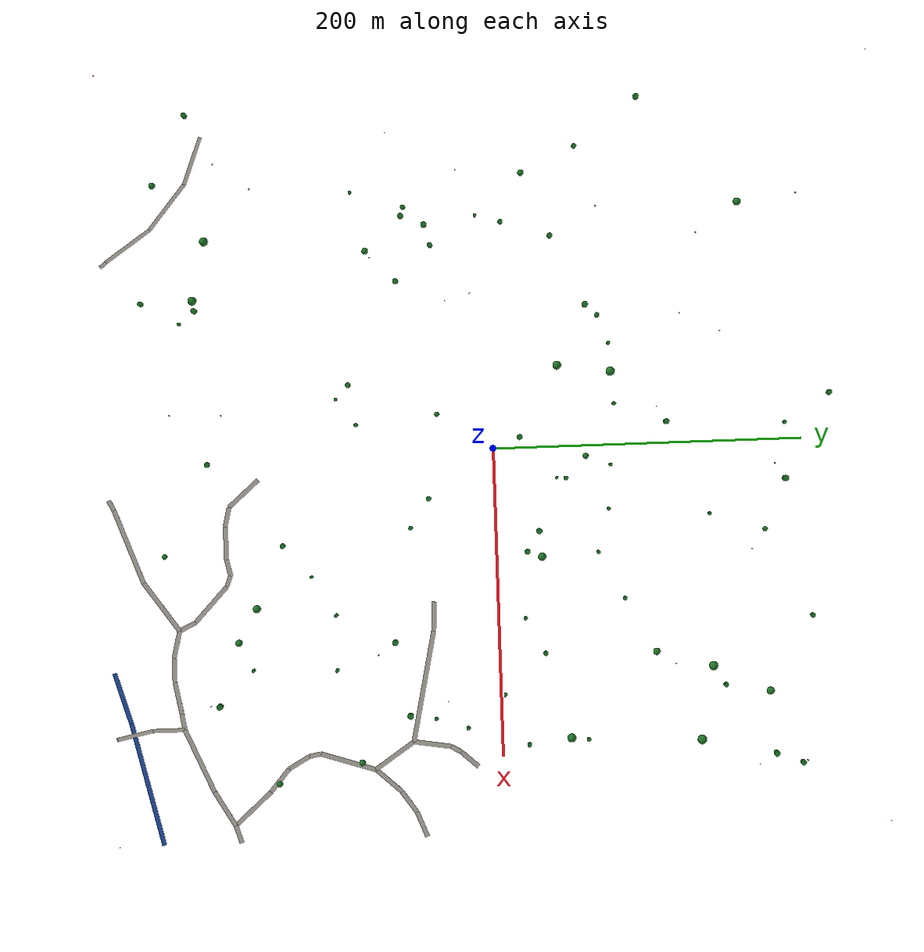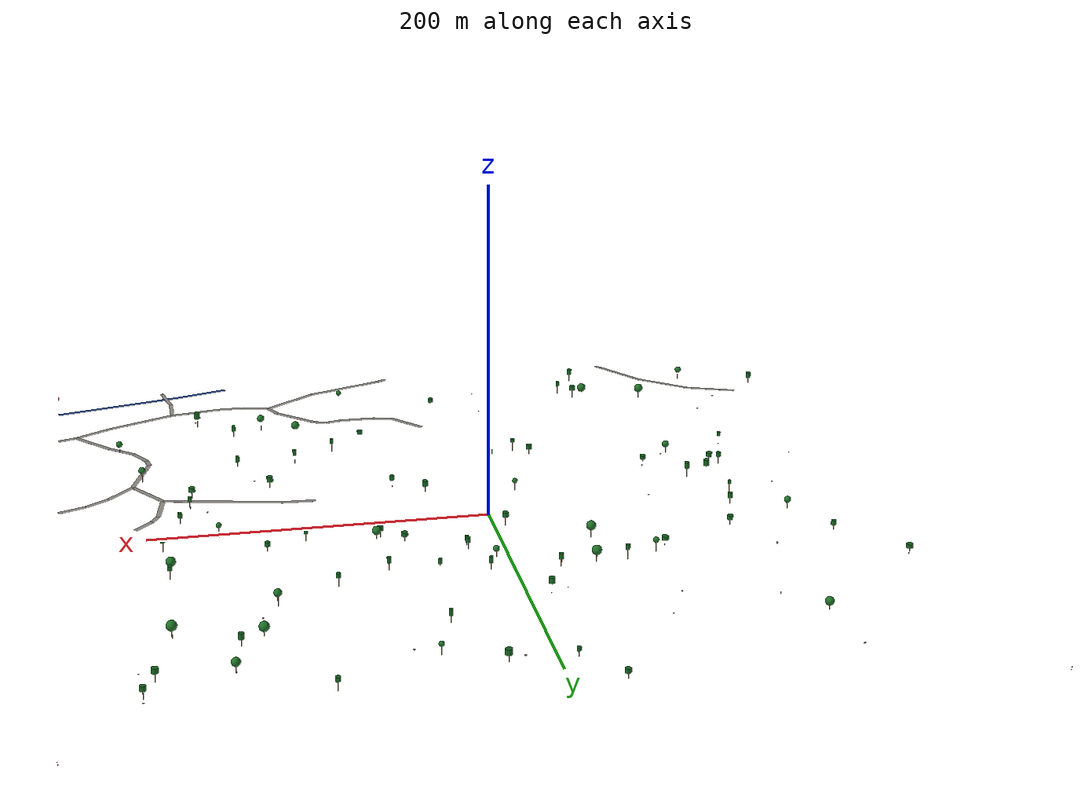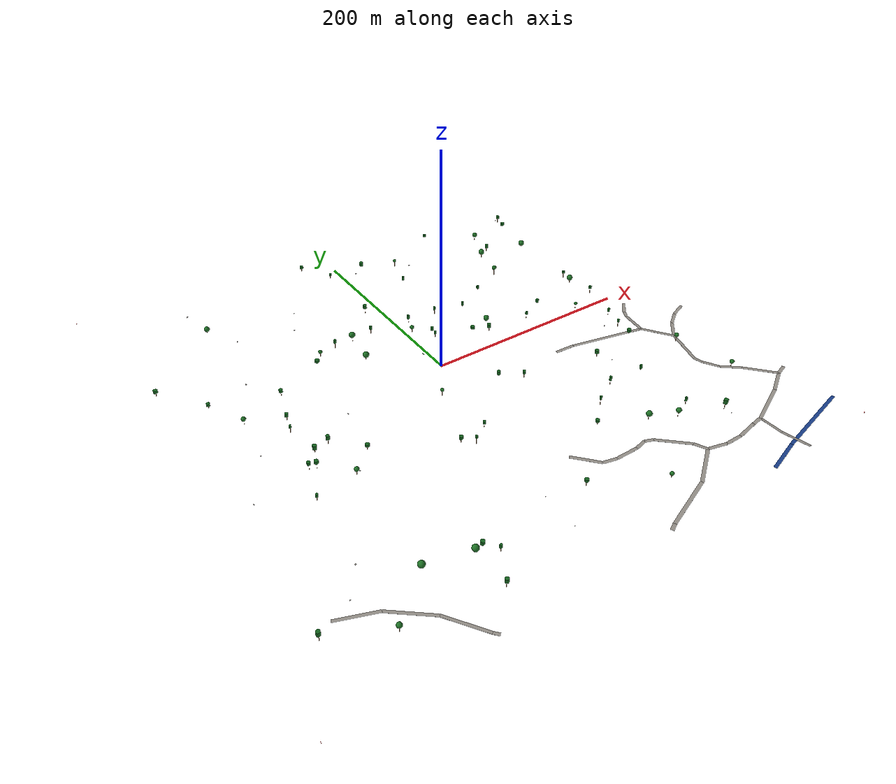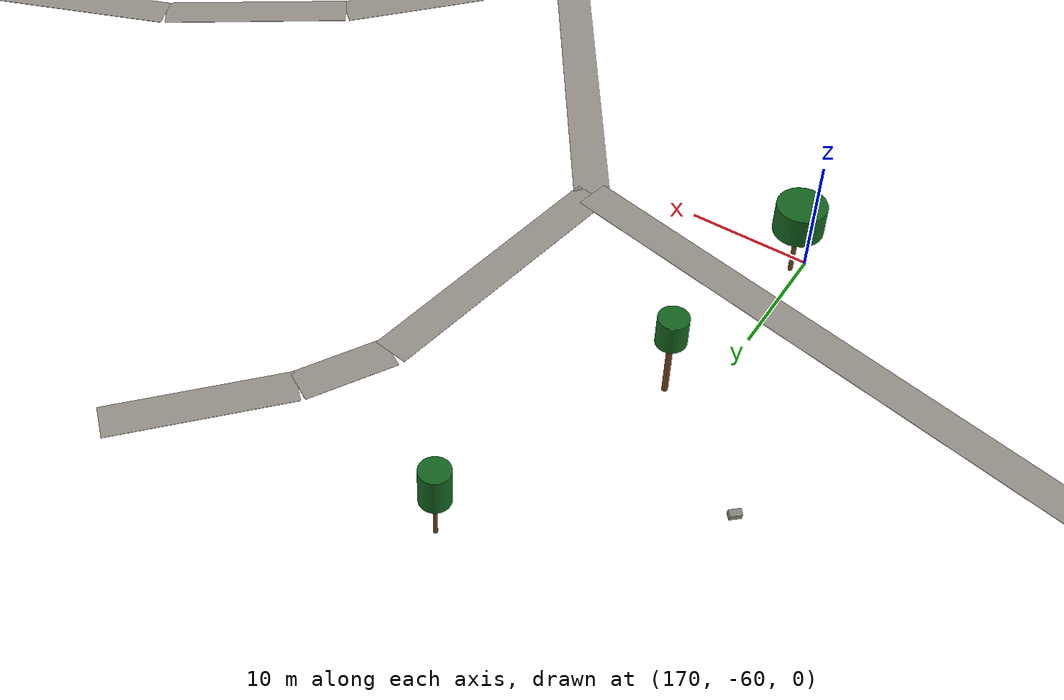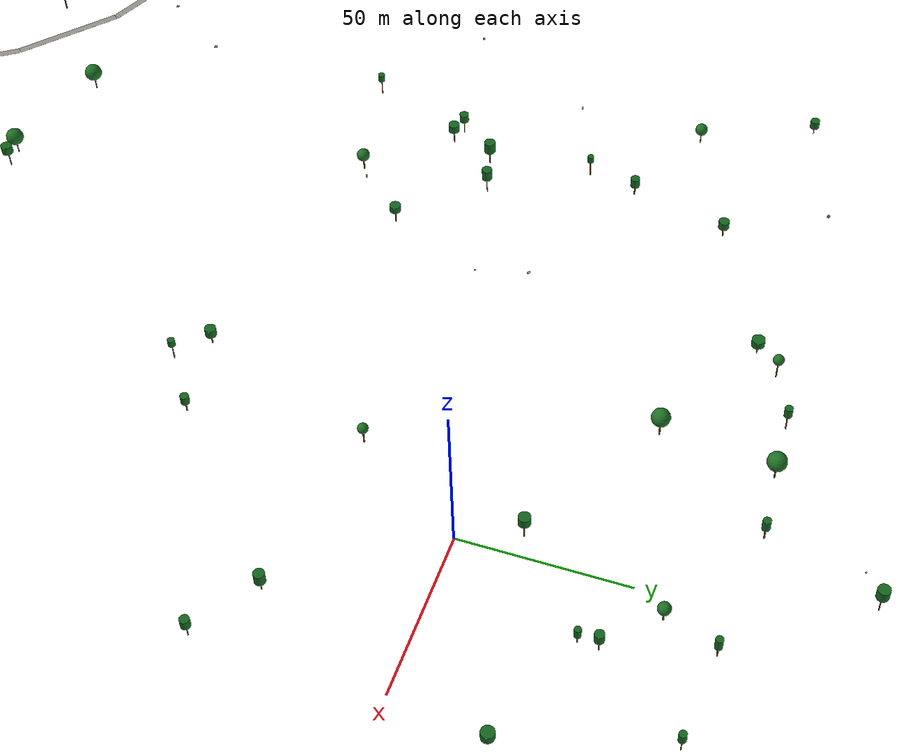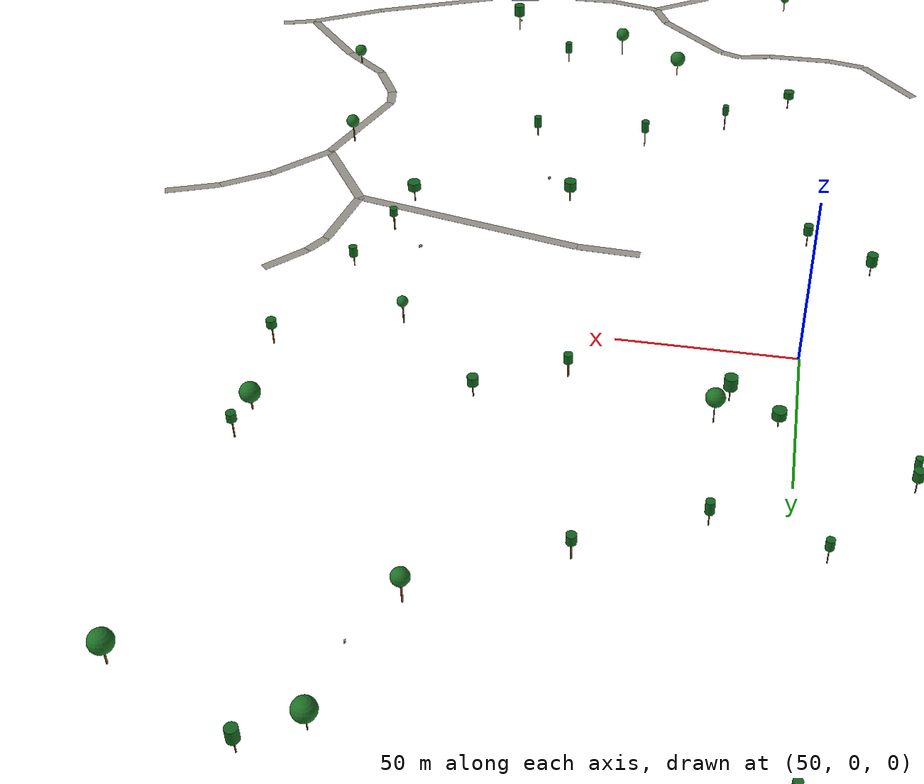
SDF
<sdf version="1.9">
 <world name="yeongwol_sinil">
  <physics name="default_physics" type="ode">
   <max_step_size>0.001</max_step_size>
   <real_time_factor>1.0</real_time_factor>
   <real_time_update_rate>1000</real_time_update_rate>
  </physics>
  <gravity>0 0 -9.81</gravity>
  <spherical_coordinates>
   <surface_model>EARTH_WGS84</surface_model>
   <world_frame_orientation>ENU</world_frame_orientation>
   <latitude_deg>37.2599</latitude_deg>
   <longitude_deg>128.2404</longitude_deg>
   <elevation>289.0</elevation>
   <heading_deg>0</heading_deg>
  </spherical_coordinates>
  <light type="directional" name="sun">
   <pose>0 0 100 0 0 0</pose>
   <diffuse>0.9 0.9 0.85 1</diffuse>
   <specular>0.3 0.3 0.3 1</specular>
   <direction>-0.5 0.3 -1.0</direction>
  </light>
  <light type="directional" name="ambient_light">
   <cast_shadows>false</cast_shadows>
   <pose>0 0 50 0 0 0</pose>
   <diffuse>0.3 0.3 0.35 1</diffuse>
   <specular>0.05 0.05 0.05 1</specular>
   <direction>0.2 -0.3 -1.0</direction>
  </light>
  <model name="road_0">
   <static>true</static>
   <pose>178.0 -238.0 0.02 0 0 -1.3556</pose>
   <link name="link">
    <collision name="collision">
     <geometry><box><size>23.4 2.5 0.04</size></box></geometry>
     <surface><friction><ode><mu>0.9</mu><mu2>0.9</mu2></ode></friction></surface>
    </collision>
    <visual name="visual">
     <geometry><box><size>23.4 2.5 0.04</size></box></geometry>
     <material><ambient>0.5 0.48 0.45 1</ambient><diffuse>0.6 0.58 0.55 1</diffuse></material>
    </visual>
   </link>
  </model>
  <model name="road_1">
   <static>true</static>
   <pose>175.5 -216.2 0.02 0 0 -1.5708</pose>
   <link name="link">
    <collision name="collision">
     <geometry><box><size>21.0 2.5 0.04</size></box></geometry>
     <surface><friction><ode><mu>0.9</mu><mu2>0.9</mu2></ode></friction></surface>
    </collision>
    <visual name="visual">
     <geometry><box><size>21.0 2.5 0.04</size></box></geometry>
     <material><ambient>0.5 0.48 0.45 1</ambient><diffuse>0.6 0.58 0.55 1</diffuse></material>
    </visual>
   </link>
  </model>
  <model name="road_2">
   <static>true</static>
   <pose>28.6 -248.4 0.02 0 0 0.4773</pose>
   <link name="link">
    <collision name="collision">
     <geometry><box><size>7.0 3.0 0.04</size></box></geometry>
     <surface><friction><ode><mu>0.9</mu><mu2>0.9</mu2></ode></friction></surface>
    </collision>
    <visual name="visual">
     <geometry><box><size>7.0 3.0 0.04</size></box></geometry>
     <material><ambient>0.5 0.48 0.45 1</ambient><diffuse>0.6 0.58 0.55 1</diffuse></material>
    </visual>
   </link>
  </model>
  <model name="road_3">
   <static>true</static>
   <pose>55.6 -238.0 0.02 0 0 0.3528</pose>
   <link name="link">
    <collision name="collision">
     <geometry><box><size>50.9 3.0 0.04</size></box></geometry>
     <surface><friction><ode><mu>0.9</mu><mu2>0.9</mu2></ode></friction></surface>
    </collision>
    <visual name="visual">
     <geometry><box><size>50.9 3.0 0.04</size></box></geometry>
     <material><ambient>0.5 0.48 0.45 1</ambient><diffuse>0.6 0.58 0.55 1</diffuse></material>
    </visual>
   </link>
  </model>
  <model name="road_4">
   <static>true</static>
   <pose>95.4 -218.0 0.02 0 0 0.6118</pose>
   <link name="link">
    <collision name="collision">
     <geometry><box><size>38.9 3.0 0.04</size></box></geometry>
     <surface><friction><ode><mu>0.9</mu><mu2>0.9</mu2></ode></friction></surface>
    </collision>
    <visual name="visual">
     <geometry><box><size>38.9 3.0 0.04</size></box></geometry>
     <material><ambient>0.5 0.48 0.45 1</ambient><diffuse>0.6 0.58 0.55 1</diffuse></material>
    </visual>
   </link>
  </model>
  <model name="road_5">
   <static>true</static>
   <pose>180.5 -249.7 0.02 0 0 -1.4811</pose>
   <link name="link">
    <collision name="collision">
     <geometry><box><size>0.5 2.5 0.04</size></box></geometry>
     <surface><friction><ode><mu>0.9</mu><mu2>0.9</mu2></ode></friction></surface>
    </collision>
    <visual name="visual">
     <geometry><box><size>0.5 2.5 0.04</size></box></geometry>
     <material><ambient>0.5 0.48 0.45 1</ambient><diffuse>0.6 0.58 0.55 1</diffuse></material>
    </visual>
   </link>
  </model>
  <model name="road_6">
   <static>true</static>
   <pose>120.1 -209.0 0.02 0 0 -0.2390</pose>
   <link name="link">
    <collision name="collision">
     <geometry><box><size>18.1 3.0 0.04</size></box></geometry>
     <surface><friction><ode><mu>0.9</mu><mu2>0.9</mu2></ode></friction></surface>
    </collision>
    <visual name="visual">
     <geometry><box><size>18.1 3.0 0.04</size></box></geometry>
     <material><ambient>0.5 0.48 0.45 1</ambient><diffuse>0.6 0.58 0.55 1</diffuse></material>
    </visual>
   </link>
  </model>
  <model name="road_7">
   <static>true</static>
   <pose>136.8 -211.1 0.02 0 0 0.0000</pose>
   <link name="link">
    <collision name="collision">
     <geometry><box><size>15.7 3.0 0.04</size></box></geometry>
     <surface><friction><ode><mu>0.9</mu><mu2>0.9</mu2></ode></friction></surface>
    </collision>
    <visual name="visual">
     <geometry><box><size>15.7 3.0 0.04</size></box></geometry>
     <material><ambient>0.5 0.48 0.45 1</ambient><diffuse>0.6 0.58 0.55 1</diffuse></material>
    </visual>
   </link>
  </model>
  <model name="road_8">
   <static>true</static>
   <pose>154.8 -209.2 0.02 0 0 0.1842</pose>
   <link name="link">
    <collision name="collision">
     <geometry><box><size>20.8 3.0 0.04</size></box></geometry>
     <surface><friction><ode><mu>0.9</mu><mu2>0.9</mu2></ode></friction></surface>
    </collision>
    <visual name="visual">
     <geometry><box><size>20.8 3.0 0.04</size></box></geometry>
     <material><ambient>0.5 0.48 0.45 1</ambient><diffuse>0.6 0.58 0.55 1</diffuse></material>
    </visual>
   </link>
  </model>
  <model name="road_9">
   <static>true</static>
   <pose>170.3 -206.5 0.02 0 0 0.1575</pose>
   <link name="link">
    <collision name="collision">
     <geometry><box><size>10.6 3.0 0.04</size></box></geometry>
     <surface><friction><ode><mu>0.9</mu><mu2>0.9</mu2></ode></friction></surface>
    </collision>
    <visual name="visual">
     <geometry><box><size>10.6 3.0 0.04</size></box></geometry>
     <material><ambient>0.5 0.48 0.45 1</ambient><diffuse>0.6 0.58 0.55 1</diffuse></material>
    </visual>
   </link>
  </model>
  <model name="road_10">
   <static>true</static>
   <pose>108.9 -201.7 0.02 0 0 2.0188</pose>
   <link name="link">
    <collision name="collision">
     <geometry><box><size>11.5 3.0 0.04</size></box></geometry>
     <surface><friction><ode><mu>0.9</mu><mu2>0.9</mu2></ode></friction></surface>
    </collision>
    <visual name="visual">
     <geometry><box><size>11.5 3.0 0.04</size></box></geometry>
     <material><ambient>0.5 0.48 0.45 1</ambient><diffuse>0.6 0.58 0.55 1</diffuse></material>
    </visual>
   </link>
  </model>
  <model name="road_11">
   <static>true</static>
   <pose>95.1 -185.9 0.02 0 0 2.3888</pose>
   <link name="link">
    <collision name="collision">
     <geometry><box><size>30.9 3.0 0.04</size></box></geometry>
     <surface><friction><ode><mu>0.9</mu><mu2>0.9</mu2></ode></friction></surface>
    </collision>
    <visual name="visual">
     <geometry><box><size>30.9 3.0 0.04</size></box></geometry>
     <material><ambient>0.5 0.48 0.45 1</ambient><diffuse>0.6 0.58 0.55 1</diffuse></material>
    </visual>
   </link>
  </model>
  <model name="road_12">
   <static>true</static>
   <pose>80.2 -174.0 0.02 0 0 2.7828</pose>
   <link name="link">
    <collision name="collision">
     <geometry><box><size>7.6 3.0 0.04</size></box></geometry>
     <surface><friction><ode><mu>0.9</mu><mu2>0.9</mu2></ode></friction></surface>
    </collision>
    <visual name="visual">
     <geometry><box><size>7.6 3.0 0.04</size></box></geometry>
     <material><ambient>0.5 0.48 0.45 1</ambient><diffuse>0.6 0.58 0.55 1</diffuse></material>
    </visual>
   </link>
  </model>
  <model name="road_13">
   <static>true</static>
   <pose>71.4 -173.8 0.02 0 0 -2.9176</pose>
   <link name="link">
    <collision name="collision">
     <geometry><box><size>10.7 3.0 0.04</size></box></geometry>
     <surface><friction><ode><mu>0.9</mu><mu2>0.9</mu2></ode></friction></surface>
    </collision>
    <visual name="visual">
     <geometry><box><size>10.7 3.0 0.04</size></box></geometry>
     <material><ambient>0.5 0.48 0.45 1</ambient><diffuse>0.6 0.58 0.55 1</diffuse></material>
    </visual>
   </link>
  </model>
  <model name="road_14">
   <static>true</static>
   <pose>55.5 -175.0 0.02 0 0 3.1416</pose>
   <link name="link">
    <collision name="collision">
     <geometry><box><size>21.4 3.0 0.04</size></box></geometry>
     <surface><friction><ode><mu>0.9</mu><mu2>0.9</mu2></ode></friction></surface>
    </collision>
    <visual name="visual">
     <geometry><box><size>21.4 3.0 0.04</size></box></geometry>
     <material><ambient>0.5 0.48 0.45 1</ambient><diffuse>0.6 0.58 0.55 1</diffuse></material>
    </visual>
   </link>
  </model>
  <model name="road_15">
   <static>true</static>
   <pose>38.6 -173.6 0.02 0 0 2.9141</pose>
   <link name="link">
    <collision name="collision">
     <geometry><box><size>12.7 3.0 0.04</size></box></geometry>
     <surface><friction><ode><mu>0.9</mu><mu2>0.9</mu2></ode></friction></surface>
    </collision>
    <visual name="visual">
     <geometry><box><size>12.7 3.0 0.04</size></box></geometry>
     <material><ambient>0.5 0.48 0.45 1</ambient><diffuse>0.6 0.58 0.55 1</diffuse></material>
    </visual>
   </link>
  </model>
  <model name="road_16">
   <static>true</static>
   <pose>23.9 -162.4 0.02 0 0 2.2914</pose>
   <link name="link">
    <collision name="collision">
     <geometry><box><size>25.9 3.0 0.04</size></box></geometry>
     <surface><friction><ode><mu>0.9</mu><mu2>0.9</mu2></ode></friction></surface>
    </collision>
    <visual name="visual">
     <geometry><box><size>25.9 3.0 0.04</size></box></geometry>
     <material><ambient>0.5 0.48 0.45 1</ambient><diffuse>0.6 0.58 0.55 1</diffuse></material>
    </visual>
   </link>
  </model>
  <model name="road_17">
   <static>true</static>
   <pose>190.2 -45.7 0.02 0 0 1.4122</pose>
   <link name="link">
    <collision name="collision">
     <geometry><box><size>24.1 3.0 0.04</size></box></geometry>
     <surface><friction><ode><mu>0.9</mu><mu2>0.9</mu2></ode></friction></surface>
    </collision>
    <visual name="visual">
     <geometry><box><size>24.1 3.0 0.04</size></box></geometry>
     <material><ambient>0.5 0.48 0.45 1</ambient><diffuse>0.6 0.58 0.55 1</diffuse></material>
    </visual>
   </link>
  </model>
  <model name="road_18">
   <static>true</static>
   <pose>194.0 -30.5 0.02 0 0 1.0520</pose>
   <link name="link">
    <collision name="collision">
     <geometry><box><size>7.7 3.0 0.04</size></box></geometry>
     <surface><friction><ode><mu>0.9</mu><mu2>0.9</mu2></ode></friction></surface>
    </collision>
    <visual name="visual">
     <geometry><box><size>7.7 3.0 0.04</size></box></geometry>
     <material><ambient>0.5 0.48 0.45 1</ambient><diffuse>0.6 0.58 0.55 1</diffuse></material>
    </visual>
   </link>
  </model>
  <model name="road_19">
   <static>true</static>
   <pose>200.9 -21.7 0.02 0 0 0.8306</pose>
   <link name="link">
    <collision name="collision">
     <geometry><box><size>14.8 3.0 0.04</size></box></geometry>
     <surface><friction><ode><mu>0.9</mu><mu2>0.9</mu2></ode></friction></surface>
    </collision>
    <visual name="visual">
     <geometry><box><size>14.8 3.0 0.04</size></box></geometry>
     <material><ambient>0.5 0.48 0.45 1</ambient><diffuse>0.6 0.58 0.55 1</diffuse></material>
    </visual>
   </link>
  </model>
  <model name="road_20">
   <static>true</static>
   <pose>152.7 -50.0 0.02 0 0 2.9315</pose>
   <link name="link">
    <collision name="collision">
     <geometry><box><size>72.9 3.0 0.04</size></box></geometry>
     <surface><friction><ode><mu>0.9</mu><mu2>0.9</mu2></ode></friction></surface>
    </collision>
    <visual name="visual">
     <geometry><box><size>72.9 3.0 0.04</size></box></geometry>
     <material><ambient>0.5 0.48 0.45 1</ambient><diffuse>0.6 0.58 0.55 1</diffuse></material>
    </visual>
   </link>
  </model>
  <model name="road_21">
   <static>true</static>
   <pose>107.5 -41.9 0.02 0 0 3.0913</pose>
   <link name="link">
    <collision name="collision">
     <geometry><box><size>19.0 3.0 0.04</size></box></geometry>
     <surface><friction><ode><mu>0.9</mu><mu2>0.9</mu2></ode></friction></surface>
    </collision>
    <visual name="visual">
     <geometry><box><size>19.0 3.0 0.04</size></box></geometry>
     <material><ambient>0.5 0.48 0.45 1</ambient><diffuse>0.6 0.58 0.55 1</diffuse></material>
    </visual>
   </link>
  </model>
  <model name="road_22">
   <static>true</static>
   <pose>196.9 -70.2 0.02 0 0 2.1674</pose>
   <link name="link">
    <collision name="collision">
     <geometry><box><size>30.5 3.0 0.04</size></box></geometry>
     <surface><friction><ode><mu>0.9</mu><mu2>0.9</mu2></ode></friction></surface>
    </collision>
    <visual name="visual">
     <geometry><box><size>30.5 3.0 0.04</size></box></geometry>
     <material><ambient>0.5 0.48 0.45 1</ambient><diffuse>0.6 0.58 0.55 1</diffuse></material>
    </visual>
   </link>
  </model>
  <model name="road_23">
   <static>true</static>
   <pose>227.6 -181.3 0.02 0 0 -2.6122</pose>
   <link name="link">
    <collision name="collision">
     <geometry><box><size>25.9 3.0 0.04</size></box></geometry>
     <surface><friction><ode><mu>0.9</mu><mu2>0.9</mu2></ode></friction></surface>
    </collision>
    <visual name="visual">
     <geometry><box><size>25.9 3.0 0.04</size></box></geometry>
     <material><ambient>0.5 0.48 0.45 1</ambient><diffuse>0.6 0.58 0.55 1</diffuse></material>
    </visual>
   </link>
  </model>
  <model name="road_24">
   <static>true</static>
   <pose>195.9 -196.8 0.02 0 0 -2.7305</pose>
   <link name="link">
    <collision name="collision">
     <geometry><box><size>44.6 3.0 0.04</size></box></geometry>
     <surface><friction><ode><mu>0.9</mu><mu2>0.9</mu2></ode></friction></surface>
    </collision>
    <visual name="visual">
     <geometry><box><size>44.6 3.0 0.04</size></box></geometry>
     <material><ambient>0.5 0.48 0.45 1</ambient><diffuse>0.6 0.58 0.55 1</diffuse></material>
    </visual>
   </link>
  </model>
  <model name="road_25">
   <static>true</static>
   <pose>244.4 -173.0 0.02 0 0 0.3102</pose>
   <link name="link">
    <collision name="collision">
     <geometry><box><size>11.8 3.0 0.04</size></box></geometry>
     <surface><friction><ode><mu>0.9</mu><mu2>0.9</mu2></ode></friction></surface>
    </collision>
    <visual name="visual">
     <geometry><box><size>11.8 3.0 0.04</size></box></geometry>
     <material><ambient>0.5 0.48 0.45 1</ambient><diffuse>0.6 0.58 0.55 1</diffuse></material>
    </visual>
   </link>
  </model>
  <model name="road_26">
   <static>true</static>
   <pose>-192.8 -188.3 0.02 0 0 -0.3589</pose>
   <link name="link">
    <collision name="collision">
     <geometry><box><size>32.5 2.5 0.04</size></box></geometry>
     <surface><friction><ode><mu>0.9</mu><mu2>0.9</mu2></ode></friction></surface>
    </collision>
    <visual name="visual">
     <geometry><box><size>32.5 2.5 0.04</size></box></geometry>
     <material><ambient>0.5 0.48 0.45 1</ambient><diffuse>0.6 0.58 0.55 1</diffuse></material>
    </visual>
   </link>
  </model>
  <model name="road_27">
   <static>true</static>
   <pose>-163.4 -205.7 0.02 0 0 -0.6848</pose>
   <link name="link">
    <collision name="collision">
     <geometry><box><size>36.8 2.5 0.04</size></box></geometry>
     <surface><friction><ode><mu>0.9</mu><mu2>0.9</mu2></ode></friction></surface>
    </collision>
    <visual name="visual">
     <geometry><box><size>36.8 2.5 0.04</size></box></geometry>
     <material><ambient>0.5 0.48 0.45 1</ambient><diffuse>0.6 0.58 0.55 1</diffuse></material>
    </visual>
   </link>
  </model>
  <model name="road_28">
   <static>true</static>
   <pose>-139.1 -231.8 0.02 0 0 -0.9678</pose>
   <link name="link">
    <collision name="collision">
     <geometry><box><size>35.2 2.5 0.04</size></box></geometry>
     <surface><friction><ode><mu>0.9</mu><mu2>0.9</mu2></ode></friction></surface>
    </collision>
    <visual name="visual">
     <geometry><box><size>35.2 2.5 0.04</size></box></geometry>
     <material><ambient>0.5 0.48 0.45 1</ambient><diffuse>0.6 0.58 0.55 1</diffuse></material>
    </visual>
   </link>
  </model>
  <model name="road_29">
   <static>true</static>
   <pose>-127.5 -248.2 0.02 0 0 -0.8351</pose>
   <link name="link">
    <collision name="collision">
     <geometry><box><size>5.0 2.5 0.04</size></box></geometry>
     <surface><friction><ode><mu>0.9</mu><mu2>0.9</mu2></ode></friction></surface>
    </collision>
    <visual name="visual">
     <geometry><box><size>5.0 2.5 0.04</size></box></geometry>
     <material><ambient>0.5 0.48 0.45 1</ambient><diffuse>0.6 0.58 0.55 1</diffuse></material>
    </visual>
   </link>
  </model>
  <model name="road_30">
   <static>true</static>
   <pose>242.0 -54.0 0.02 0 0 -2.7693</pose>
   <link name="link">
    <collision name="collision">
     <geometry><box><size>17.2 3.0 0.04</size></box></geometry>
     <surface><friction><ode><mu>0.9</mu><mu2>0.9</mu2></ode></friction></surface>
    </collision>
    <visual name="visual">
     <geometry><box><size>17.2 3.0 0.04</size></box></geometry>
     <material><ambient>0.5 0.48 0.45 1</ambient><diffuse>0.6 0.58 0.55 1</diffuse></material>
    </visual>
   </link>
  </model>
  <model name="road_31">
   <static>true</static>
   <pose>227.1 -61.9 0.02 0 0 -2.5379</pose>
   <link name="link">
    <collision name="collision">
     <geometry><box><size>16.7 3.0 0.04</size></box></geometry>
     <surface><friction><ode><mu>0.9</mu><mu2>0.9</mu2></ode></friction></surface>
    </collision>
    <visual name="visual">
     <geometry><box><size>16.7 3.0 0.04</size></box></geometry>
     <material><ambient>0.5 0.48 0.45 1</ambient><diffuse>0.6 0.58 0.55 1</diffuse></material>
    </visual>
   </link>
  </model>
  <model name="road_32">
   <static>true</static>
   <pose>212.8 -74.7 0.02 0 0 -2.3100</pose>
   <link name="link">
    <collision name="collision">
     <geometry><box><size>21.9 3.0 0.04</size></box></geometry>
     <surface><friction><ode><mu>0.9</mu><mu2>0.9</mu2></ode></friction></surface>
    </collision>
    <visual name="visual">
     <geometry><box><size>21.9 3.0 0.04</size></box></geometry>
     <material><ambient>0.5 0.48 0.45 1</ambient><diffuse>0.6 0.58 0.55 1</diffuse></material>
    </visual>
   </link>
  </model>
  <model name="road_33">
   <static>true</static>
   <pose>199.8 -100.4 0.02 0 0 -1.8843</pose>
   <link name="link">
    <collision name="collision">
     <geometry><box><size>37.0 3.0 0.04</size></box></geometry>
     <surface><friction><ode><mu>0.9</mu><mu2>0.9</mu2></ode></friction></surface>
    </collision>
    <visual name="visual">
     <geometry><box><size>37.0 3.0 0.04</size></box></geometry>
     <material><ambient>0.5 0.48 0.45 1</ambient><diffuse>0.6 0.58 0.55 1</diffuse></material>
    </visual>
   </link>
  </model>
  <model name="road_34">
   <static>true</static>
   <pose>194.8 -121.8 0.02 0 0 -1.3853</pose>
   <link name="link">
    <collision name="collision">
     <geometry><box><size>7.7 3.0 0.04</size></box></geometry>
     <surface><friction><ode><mu>0.9</mu><mu2>0.9</mu2></ode></friction></surface>
    </collision>
    <visual name="visual">
     <geometry><box><size>7.7 3.0 0.04</size></box></geometry>
     <material><ambient>0.5 0.48 0.45 1</ambient><diffuse>0.6 0.58 0.55 1</diffuse></material>
    </visual>
   </link>
  </model>
  <model name="road_35">
   <static>true</static>
   <pose>199.3 -132.2 0.02 0 0 -1.0520</pose>
   <link name="link">
    <collision name="collision">
     <geometry><box><size>15.3 3.0 0.04</size></box></geometry>
     <surface><friction><ode><mu>0.9</mu><mu2>0.9</mu2></ode></friction></surface>
    </collision>
    <visual name="visual">
     <geometry><box><size>15.3 3.0 0.04</size></box></geometry>
     <material><ambient>0.5 0.48 0.45 1</ambient><diffuse>0.6 0.58 0.55 1</diffuse></material>
    </visual>
   </link>
  </model>
  <model name="road_36">
   <static>true</static>
   <pose>210.4 -145.1 0.02 0 0 -0.6979</pose>
   <link name="link">
    <collision name="collision">
     <geometry><box><size>19.2 3.0 0.04</size></box></geometry>
     <surface><friction><ode><mu>0.9</mu><mu2>0.9</mu2></ode></friction></surface>
    </collision>
    <visual name="visual">
     <geometry><box><size>19.2 3.0 0.04</size></box></geometry>
     <material><ambient>0.5 0.48 0.45 1</ambient><diffuse>0.6 0.58 0.55 1</diffuse></material>
    </visual>
   </link>
  </model>
  <model name="road_37">
   <static>true</static>
   <pose>228.3 -163.0 0.02 0 0 -0.8444</pose>
   <link name="link">
    <collision name="collision">
     <geometry><box><size>31.5 3.0 0.04</size></box></geometry>
     <surface><friction><ode><mu>0.9</mu><mu2>0.9</mu2></ode></friction></surface>
    </collision>
    <visual name="visual">
     <geometry><box><size>31.5 3.0 0.04</size></box></geometry>
     <material><ambient>0.5 0.48 0.45 1</ambient><diffuse>0.6 0.58 0.55 1</diffuse></material>
    </visual>
   </link>
  </model>
  <model name="water_0">
   <static>true</static>
   <pose>153.9 -245.1 -0.15 0 0 0.2915</pose>
   <link name="link">
    <visual name="visual">
     <geometry><box><size>34.3 3.0 0.02</size></box></geometry>
     <material><ambient>0.05 0.15 0.4 0.9</ambient><diffuse>0.1 0.25 0.55 0.9</diffuse></material>
    </visual>
   </link>
  </model>
  <model name="water_1">
   <static>true</static>
   <pose>210.1 -230.8 -0.15 0 0 0.2305</pose>
   <link name="link">
    <visual name="visual">
     <geometry><box><size>81.9 3.0 0.02</size></box></geometry>
     <material><ambient>0.05 0.15 0.4 0.9</ambient><diffuse>0.1 0.25 0.55 0.9</diffuse></material>
    </visual>
   </link>
  </model>
  <model name="tree_0">
   <static>true</static>
   <pose>62.7 -213.7 1.9 0 0 4.65</pose>
   <link name="link">
    <collision name="trunk_col">
     <geometry><cylinder><radius>0.14</radius><length>3.7</length></cylinder></geometry>
    </collision>
    <visual name="trunk">
     <geometry><cylinder><radius>0.14</radius><length>3.7</length></cylinder></geometry>
     <material><ambient>0.35 0.2 0.08 1</ambient><diffuse>0.45 0.28 0.12 1</diffuse></material>
    </visual>
    <visual name="canopy">
     <pose>0 0 3.5 0 0 0</pose>
     <geometry><sphere><radius>1.7</radius></sphere></geometry>
     <material><ambient>0.08 0.35 0.1 1</ambient><diffuse>0.12 0.45 0.15 1</diffuse></material>
    </visual>
   </link>
  </model>
  <model name="tree_1">
   <static>true</static>
   <pose>20.4 40.7 1.5 0 0 1.25</pose>
   <link name="link">
    <collision name="trunk_col">
     <geometry><cylinder><radius>0.15</radius><length>3.1</length></cylinder></geometry>
    </collision>
    <visual name="trunk">
     <geometry><cylinder><radius>0.15</radius><length>3.1</length></cylinder></geometry>
     <material><ambient>0.35 0.2 0.08 1</ambient><diffuse>0.45 0.28 0.12 1</diffuse></material>
    </visual>
    <visual name="canopy">
     <pose>0 0 3.1 0 0 0</pose>
     <geometry><cylinder><radius>1.0</radius><length>3.0</length></cylinder></geometry>
     <material><ambient>0.05 0.3 0.08 1</ambient><diffuse>0.08 0.4 0.12 1</diffuse></material>
    </visual>
   </link>
  </model>
  <model name="tree_2">
   <static>true</static>
   <pose>67.4 20.2 2.2 0 0 1.00</pose>
   <link name="link">
    <collision name="trunk_col">
     <geometry><cylinder><radius>0.16</radius><length>4.3</length></cylinder></geometry>
    </collision>
    <visual name="trunk">
     <geometry><cylinder><radius>0.16</radius><length>4.3</length></cylinder></geometry>
     <material><ambient>0.35 0.2 0.08 1</ambient><diffuse>0.45 0.28 0.12 1</diffuse></material>
    </visual>
    <visual name="canopy">
     <pose>0 0 4.0 0 0 0</pose>
     <geometry><cylinder><radius>1.8</radius><length>3.7</length></cylinder></geometry>
     <material><ambient>0.05 0.3 0.08 1</ambient><diffuse>0.08 0.4 0.12 1</diffuse></material>
    </visual>
   </link>
  </model>
  <model name="tree_3">
   <static>true</static>
   <pose>-34.8 -100.0 2.9 0 0 5.32</pose>
   <link name="link">
    <collision name="trunk_col">
     <geometry><cylinder><radius>0.16</radius><length>5.9</length></cylinder></geometry>
    </collision>
    <visual name="trunk">
     <geometry><cylinder><radius>0.16</radius><length>5.9</length></cylinder></geometry>
     <material><ambient>0.35 0.2 0.08 1</ambient><diffuse>0.45 0.28 0.12 1</diffuse></material>
    </visual>
    <visual name="canopy">
     <pose>0 0 4.0 0 0 0</pose>
     <geometry><cylinder><radius>1.1</radius><length>2.2</length></cylinder></geometry>
     <material><ambient>0.05 0.3 0.08 1</ambient><diffuse>0.08 0.4 0.12 1</diffuse></material>
    </visual>
   </link>
  </model>
  <model name="tree_4">
   <static>true</static>
   <pose>46.7 138.2 2.2 0 0 1.84</pose>
   <link name="link">
    <collision name="trunk_col">
     <geometry><cylinder><radius>0.14</radius><length>4.4</length></cylinder></geometry>
    </collision>
    <visual name="trunk">
     <geometry><cylinder><radius>0.14</radius><length>4.4</length></cylinder></geometry>
     <material><ambient>0.35 0.2 0.08 1</ambient><diffuse>0.45 0.28 0.12 1</diffuse></material>
    </visual>
    <visual name="canopy">
     <pose>0 0 4.1 0 0 0</pose>
     <geometry><cylinder><radius>1.1</radius><length>3.8</length></cylinder></geometry>
     <material><ambient>0.05 0.3 0.08 1</ambient><diffuse>0.08 0.4 0.12 1</diffuse></material>
    </visual>
   </link>
  </model>
  <model name="tree_5">
   <static>true</static>
   <pose>57.9 173.5 2.4 0 0 1.43</pose>
   <link name="link">
    <collision name="trunk_col">
     <geometry><cylinder><radius>0.21</radius><length>4.7</length></cylinder></geometry>
    </collision>
    <visual name="trunk">
     <geometry><cylinder><radius>0.21</radius><length>4.7</length></cylinder></geometry>
     <material><ambient>0.35 0.2 0.08 1</ambient><diffuse>0.45 0.28 0.12 1</diffuse></material>
    </visual>
    <visual name="canopy">
     <pose>0 0 3.9 0 0 0</pose>
     <geometry><sphere><radius>1.6</radius></sphere></geometry>
     <material><ambient>0.08 0.35 0.1 1</ambient><diffuse>0.12 0.45 0.15 1</diffuse></material>
    </visual>
   </link>
  </model>
  <model name="tree_6">
   <static>true</static>
   <pose>-94.8 -189.1 2.8 0 0 1.02</pose>
   <link name="link">
    <collision name="trunk_col">
     <geometry><cylinder><radius>0.17</radius><length>5.6</length></cylinder></geometry>
    </collision>
    <visual name="trunk">
     <geometry><cylinder><radius>0.17</radius><length>5.6</length></cylinder></geometry>
     <material><ambient>0.35 0.2 0.08 1</ambient><diffuse>0.45 0.28 0.12 1</diffuse></material>
    </visual>
    <visual name="canopy">
     <pose>0 0 4.3 0 0 0</pose>
     <geometry><cylinder><radius>1.8</radius><length>2.9</length></cylinder></geometry>
     <material><ambient>0.05 0.3 0.08 1</ambient><diffuse>0.08 0.4 0.12 1</diffuse></material>
    </visual>
   </link>
  </model>
  <model name="tree_7">
   <static>true</static>
   <pose>-65.1 76.6 2.9 0 0 4.58</pose>
   <link name="link">
    <collision name="trunk_col">
     <geometry><cylinder><radius>0.20</radius><length>5.8</length></cylinder></geometry>
    </collision>
    <visual name="trunk">
     <geometry><cylinder><radius>0.20</radius><length>5.8</length></cylinder></geometry>
     <material><ambient>0.35 0.2 0.08 1</ambient><diffuse>0.45 0.28 0.12 1</diffuse></material>
    </visual>
    <visual name="canopy">
     <pose>0 0 4.5 0 0 0</pose>
     <geometry><cylinder><radius>1.2</radius><length>3.2</length></cylinder></geometry>
     <material><ambient>0.05 0.3 0.08 1</ambient><diffuse>0.08 0.4 0.12 1</diffuse></material>
    </visual>
   </link>
  </model>
  <model name="tree_8">
   <static>true</static>
   <pose>-151.5 -54.2 2.5 0 0 0.35</pose>
   <link name="link">
    <collision name="trunk_col">
     <geometry><cylinder><radius>0.15</radius><length>5.1</length></cylinder></geometry>
    </collision>
    <visual name="trunk">
     <geometry><cylinder><radius>0.15</radius><length>5.1</length></cylinder></geometry>
     <material><ambient>0.35 0.2 0.08 1</ambient><diffuse>0.45 0.28 0.12 1</diffuse></material>
    </visual>
    <visual name="canopy">
     <pose>0 0 3.9 0 0 0</pose>
     <geometry><cylinder><radius>1.8</radius><length>2.6</length></cylinder></geometry>
     <material><ambient>0.05 0.3 0.08 1</ambient><diffuse>0.08 0.4 0.12 1</diffuse></material>
    </visual>
   </link>
  </model>
  <model name="tree_9">
   <static>true</static>
   <pose>144.8 137.3 1.9 0 0 5.51</pose>
   <link name="link">
    <collision name="trunk_col">
     <geometry><cylinder><radius>0.15</radius><length>3.8</length></cylinder></geometry>
    </collision>
    <visual name="trunk">
     <geometry><cylinder><radius>0.15</radius><length>3.8</length></cylinder></geometry>
     <material><ambient>0.35 0.2 0.08 1</ambient><diffuse>0.45 0.28 0.12 1</diffuse></material>
    </visual>
    <visual name="canopy">
     <pose>0 0 4.8 0 0 0</pose>
     <geometry><sphere><radius>2.9</radius></sphere></geometry>
     <material><ambient>0.08 0.35 0.1 1</ambient><diffuse>0.12 0.45 0.15 1</diffuse></material>
    </visual>
   </link>
  </model>
  <model name="tree_10">
   <static>true</static>
   <pose>-83.4 69.9 2.8 0 0 0.88</pose>
   <link name="link">
    <collision name="trunk_col">
     <geometry><cylinder><radius>0.20</radius><length>5.7</length></cylinder></geometry>
    </collision>
    <visual name="trunk">
     <geometry><cylinder><radius>0.20</radius><length>5.7</length></cylinder></geometry>
     <material><ambient>0.35 0.2 0.08 1</ambient><diffuse>0.45 0.28 0.12 1</diffuse></material>
    </visual>
    <visual name="canopy">
     <pose>0 0 4.5 0 0 0</pose>
     <geometry><sphere><radius>1.7</radius></sphere></geometry>
     <material><ambient>0.08 0.35 0.1 1</ambient><diffuse>0.12 0.45 0.15 1</diffuse></material>
    </visual>
   </link>
  </model>
  <model name="tree_11">
   <static>true</static>
   <pose>110.2 17.5 2.4 0 0 6.27</pose>
   <link name="link">
    <collision name="trunk_col">
     <geometry><cylinder><radius>0.24</radius><length>4.8</length></cylinder></geometry>
    </collision>
    <visual name="trunk">
     <geometry><cylinder><radius>0.24</radius><length>4.8</length></cylinder></geometry>
     <material><ambient>0.35 0.2 0.08 1</ambient><diffuse>0.45 0.28 0.12 1</diffuse></material>
    </visual>
    <visual name="canopy">
     <pose>0 0 3.8 0 0 0</pose>
     <geometry><cylinder><radius>1.2</radius><length>2.8</length></cylinder></geometry>
     <material><ambient>0.05 0.3 0.08 1</ambient><diffuse>0.08 0.4 0.12 1</diffuse></material>
    </visual>
   </link>
  </model>
  <model name="tree_12">
   <static>true</static>
   <pose>4.3 -184.1 2.8 0 0 3.75</pose>
   <link name="link">
    <collision name="trunk_col">
     <geometry><cylinder><radius>0.14</radius><length>5.6</length></cylinder></geometry>
    </collision>
    <visual name="trunk">
     <geometry><cylinder><radius>0.14</radius><length>5.6</length></cylinder></geometry>
     <material><ambient>0.35 0.2 0.08 1</ambient><diffuse>0.45 0.28 0.12 1</diffuse></material>
    </visual>
    <visual name="canopy">
     <pose>0 0 4.0 0 0 0</pose>
     <geometry><cylinder><radius>1.7</radius><length>2.3</length></cylinder></geometry>
     <material><ambient>0.05 0.3 0.08 1</ambient><diffuse>0.08 0.4 0.12 1</diffuse></material>
    </visual>
   </link>
  </model>
  <model name="tree_13">
   <static>true</static>
   <pose>-51.9 43.1 2.3 0 0 0.07</pose>
   <link name="link">
    <collision name="trunk_col">
     <geometry><cylinder><radius>0.25</radius><length>4.6</length></cylinder></geometry>
    </collision>
    <visual name="trunk">
     <geometry><cylinder><radius>0.25</radius><length>4.6</length></cylinder></geometry>
     <material><ambient>0.35 0.2 0.08 1</ambient><diffuse>0.45 0.28 0.12 1</diffuse></material>
    </visual>
    <visual name="canopy">
     <pose>0 0 5.1 0 0 0</pose>
     <geometry><sphere><radius>2.8</radius></sphere></geometry>
     <material><ambient>0.08 0.35 0.1 1</ambient><diffuse>0.12 0.45 0.15 1</diffuse></material>
    </visual>
   </link>
  </model>
  <model name="tree_14">
   <static>true</static>
   <pose>99.3 81.8 2.6 0 0 0.99</pose>
   <link name="link">
    <collision name="trunk_col">
     <geometry><cylinder><radius>0.22</radius><length>5.3</length></cylinder></geometry>
    </collision>
    <visual name="trunk">
     <geometry><cylinder><radius>0.22</radius><length>5.3</length></cylinder></geometry>
     <material><ambient>0.35 0.2 0.08 1</ambient><diffuse>0.45 0.28 0.12 1</diffuse></material>
    </visual>
    <visual name="canopy">
     <pose>0 0 4.0 0 0 0</pose>
     <geometry><cylinder><radius>1.3</radius><length>2.7</length></cylinder></geometry>
     <material><ambient>0.05 0.3 0.08 1</ambient><diffuse>0.08 0.4 0.12 1</diffuse></material>
    </visual>
   </link>
  </model>
  <model name="tree_15">
   <static>true</static>
   <pose>-223.5 99.9 1.9 0 0 5.47</pose>
   <link name="link">
    <collision name="trunk_col">
     <geometry><cylinder><radius>0.19</radius><length>3.8</length></cylinder></geometry>
    </collision>
    <visual name="trunk">
     <geometry><cylinder><radius>0.19</radius><length>3.8</length></cylinder></geometry>
     <material><ambient>0.35 0.2 0.08 1</ambient><diffuse>0.45 0.28 0.12 1</diffuse></material>
    </visual>
    <visual name="canopy">
     <pose>0 0 3.1 0 0 0</pose>
     <geometry><cylinder><radius>1.9</radius><length>2.4</length></cylinder></geometry>
     <material><ambient>0.05 0.3 0.08 1</ambient><diffuse>0.08 0.4 0.12 1</diffuse></material>
    </visual>
   </link>
  </model>
  <model name="tree_16">
   <static>true</static>
   <pose>-90.7 62.5 1.8 0 0 5.80</pose>
   <link name="link">
    <collision name="trunk_col">
     <geometry><cylinder><radius>0.17</radius><length>3.6</length></cylinder></geometry>
    </collision>
    <visual name="trunk">
     <geometry><cylinder><radius>0.17</radius><length>3.6</length></cylinder></geometry>
     <material><ambient>0.35 0.2 0.08 1</ambient><diffuse>0.45 0.28 0.12 1</diffuse></material>
    </visual>
    <visual name="canopy">
     <pose>0 0 3.0 0 0 0</pose>
     <geometry><cylinder><radius>2.0</radius><length>2.3</length></cylinder></geometry>
     <material><ambient>0.05 0.3 0.08 1</ambient><diffuse>0.08 0.4 0.12 1</diffuse></material>
    </visual>
   </link>
  </model>
  <model name="tree_17">
   <static>true</static>
   <pose>188.3 44.5 1.5 0 0 5.23</pose>
   <link name="link">
    <collision name="trunk_col">
     <geometry><cylinder><radius>0.24</radius><length>3.1</length></cylinder></geometry>
    </collision>
    <visual name="trunk">
     <geometry><cylinder><radius>0.24</radius><length>3.1</length></cylinder></geometry>
     <material><ambient>0.35 0.2 0.08 1</ambient><diffuse>0.45 0.28 0.12 1</diffuse></material>
    </visual>
    <visual name="canopy">
     <pose>0 0 4.3 0 0 0</pose>
     <geometry><sphere><radius>2.8</radius></sphere></geometry>
     <material><ambient>0.08 0.35 0.1 1</ambient><diffuse>0.12 0.45 0.15 1</diffuse></material>
    </visual>
   </link>
  </model>
  <model name="tree_18">
   <static>true</static>
   <pose>-86.6 -198.9 2.9 0 0 4.78</pose>
   <link name="link">
    <collision name="trunk_col">
     <geometry><cylinder><radius>0.13</radius><length>5.8</length></cylinder></geometry>
    </collision>
    <visual name="trunk">
     <geometry><cylinder><radius>0.13</radius><length>5.8</length></cylinder></geometry>
     <material><ambient>0.35 0.2 0.08 1</ambient><diffuse>0.45 0.28 0.12 1</diffuse></material>
    </visual>
    <visual name="canopy">
     <pose>0 0 4.4 0 0 0</pose>
     <geometry><cylinder><radius>1.1</radius><length>3.0</length></cylinder></geometry>
     <material><ambient>0.05 0.3 0.08 1</ambient><diffuse>0.08 0.4 0.12 1</diffuse></material>
    </visual>
   </link>
  </model>
  <model name="tree_19">
   <static>true</static>
   <pose>119.6 -167.2 2.9 0 0 3.81</pose>
   <link name="link">
    <collision name="trunk_col">
     <geometry><cylinder><radius>0.14</radius><length>5.8</length></cylinder></geometry>
    </collision>
    <visual name="trunk">
     <geometry><cylinder><radius>0.14</radius><length>5.8</length></cylinder></geometry>
     <material><ambient>0.35 0.2 0.08 1</ambient><diffuse>0.45 0.28 0.12 1</diffuse></material>
    </visual>
    <visual name="canopy">
     <pose>0 0 5.2 0 0 0</pose>
     <geometry><sphere><radius>2.3</radius></sphere></geometry>
     <material><ambient>0.08 0.35 0.1 1</ambient><diffuse>0.12 0.45 0.15 1</diffuse></material>
    </visual>
   </link>
  </model>
  <model name="tree_20">
   <static>true</static>
   <pose>209.0 193.0 2.5 0 0 2.35</pose>
   <link name="link">
    <collision name="trunk_col">
     <geometry><cylinder><radius>0.21</radius><length>5.1</length></cylinder></geometry>
    </collision>
    <visual name="trunk">
     <geometry><cylinder><radius>0.21</radius><length>5.1</length></cylinder></geometry>
     <material><ambient>0.35 0.2 0.08 1</ambient><diffuse>0.45 0.28 0.12 1</diffuse></material>
    </visual>
    <visual name="canopy">
     <pose>0 0 3.9 0 0 0</pose>
     <geometry><cylinder><radius>1.7</radius><length>2.8</length></cylinder></geometry>
     <material><ambient>0.05 0.3 0.08 1</ambient><diffuse>0.08 0.4 0.12 1</diffuse></material>
    </visual>
   </link>
  </model>
  <model name="tree_21">
   <static>true</static>
   <pose>179.8 -21.8 1.8 0 0 1.38</pose>
   <link name="link">
    <collision name="trunk_col">
     <geometry><cylinder><radius>0.16</radius><length>3.7</length></cylinder></geometry>
    </collision>
    <visual name="trunk">
     <geometry><cylinder><radius>0.16</radius><length>3.7</length></cylinder></geometry>
     <material><ambient>0.35 0.2 0.08 1</ambient><diffuse>0.45 0.28 0.12 1</diffuse></material>
    </visual>
    <visual name="canopy">
     <pose>0 0 3.4 0 0 0</pose>
     <geometry><cylinder><radius>1.2</radius><length>3.2</length></cylinder></geometry>
     <material><ambient>0.05 0.3 0.08 1</ambient><diffuse>0.08 0.4 0.12 1</diffuse></material>
    </visual>
   </link>
  </model>
  <model name="tree_22">
   <static>true</static>
   <pose>-193.1 59.0 1.6 0 0 1.75</pose>
   <link name="link">
    <collision name="trunk_col">
     <geometry><cylinder><radius>0.12</radius><length>3.2</length></cylinder></geometry>
    </collision>
    <visual name="trunk">
     <geometry><cylinder><radius>0.12</radius><length>3.2</length></cylinder></geometry>
     <material><ambient>0.35 0.2 0.08 1</ambient><diffuse>0.45 0.28 0.12 1</diffuse></material>
    </visual>
    <visual name="canopy">
     <pose>0 0 2.9 0 0 0</pose>
     <geometry><cylinder><radius>1.5</radius><length>2.7</length></cylinder></geometry>
     <material><ambient>0.05 0.3 0.08 1</ambient><diffuse>0.08 0.4 0.12 1</diffuse></material>
    </visual>
   </link>
  </model>
  <model name="tree_23">
   <static>true</static>
   <pose>-6.6 17.7 2.9 0 0 5.07</pose>
   <link name="link">
    <collision name="trunk_col">
     <geometry><cylinder><radius>0.19</radius><length>5.8</length></cylinder></geometry>
    </collision>
    <visual name="trunk">
     <geometry><cylinder><radius>0.19</radius><length>5.8</length></cylinder></geometry>
     <material><ambient>0.35 0.2 0.08 1</ambient><diffuse>0.45 0.28 0.12 1</diffuse></material>
    </visual>
    <visual name="canopy">
     <pose>0 0 4.4 0 0 0</pose>
     <geometry><cylinder><radius>1.8</radius><length>2.9</length></cylinder></geometry>
     <material><ambient>0.05 0.3 0.08 1</ambient><diffuse>0.08 0.4 0.12 1</diffuse></material>
    </visual>
   </link>
  </model>
  <model name="tree_24">
   <static>true</static>
   <pose>-139.3 -181.4 2.0 0 0 0.34</pose>
   <link name="link">
    <collision name="trunk_col">
     <geometry><cylinder><radius>0.17</radius><length>4.1</length></cylinder></geometry>
    </collision>
    <visual name="trunk">
     <geometry><cylinder><radius>0.17</radius><length>4.1</length></cylinder></geometry>
     <material><ambient>0.35 0.2 0.08 1</ambient><diffuse>0.45 0.28 0.12 1</diffuse></material>
    </visual>
    <visual name="canopy">
     <pose>0 0 4.8 0 0 0</pose>
     <geometry><sphere><radius>2.8</radius></sphere></geometry>
     <material><ambient>0.08 0.35 0.1 1</ambient><diffuse>0.12 0.45 0.15 1</diffuse></material>
    </visual>
   </link>
  </model>
  <model name="tree_25">
   <static>true</static>
   <pose>69.1 65.8 2.1 0 0 1.20</pose>
   <link name="link">
    <collision name="trunk_col">
     <geometry><cylinder><radius>0.16</radius><length>4.2</length></cylinder></geometry>
    </collision>
    <visual name="trunk">
     <geometry><cylinder><radius>0.16</radius><length>4.2</length></cylinder></geometry>
     <material><ambient>0.35 0.2 0.08 1</ambient><diffuse>0.45 0.28 0.12 1</diffuse></material>
    </visual>
    <visual name="canopy">
     <pose>0 0 4.0 0 0 0</pose>
     <geometry><cylinder><radius>1.2</radius><length>3.7</length></cylinder></geometry>
     <material><ambient>0.05 0.3 0.08 1</ambient><diffuse>0.08 0.4 0.12 1</diffuse></material>
    </visual>
   </link>
  </model>
  <model name="tree_26">
   <static>true</static>
   <pose>-23.1 -35.2 2.2 0 0 5.08</pose>
   <link name="link">
    <collision name="trunk_col">
     <geometry><cylinder><radius>0.23</radius><length>4.4</length></cylinder></geometry>
    </collision>
    <visual name="trunk">
     <geometry><cylinder><radius>0.23</radius><length>4.4</length></cylinder></geometry>
     <material><ambient>0.35 0.2 0.08 1</ambient><diffuse>0.45 0.28 0.12 1</diffuse></material>
    </visual>
    <visual name="canopy">
     <pose>0 0 3.8 0 0 0</pose>
     <geometry><sphere><radius>1.6</radius></sphere></geometry>
     <material><ambient>0.08 0.35 0.1 1</ambient><diffuse>0.12 0.45 0.15 1</diffuse></material>
    </visual>
   </link>
  </model>
  <model name="tree_27">
   <static>true</static>
   <pose>160.2 -180.9 3.0 0 0 5.33</pose>
   <link name="link">
    <collision name="trunk_col">
     <geometry><cylinder><radius>0.23</radius><length>6.0</length></cylinder></geometry>
    </collision>
    <visual name="trunk">
     <geometry><cylinder><radius>0.23</radius><length>6.0</length></cylinder></geometry>
     <material><ambient>0.35 0.2 0.08 1</ambient><diffuse>0.45 0.28 0.12 1</diffuse></material>
    </visual>
    <visual name="canopy">
     <pose>0 0 5.0 0 0 0</pose>
     <geometry><cylinder><radius>1.9</radius><length>3.9</length></cylinder></geometry>
     <material><ambient>0.05 0.3 0.08 1</ambient><diffuse>0.08 0.4 0.12 1</diffuse></material>
    </visual>
   </link>
  </model>
  <model name="tree_28">
   <static>true</static>
   <pose>-150.2 -6.5 2.8 0 0 2.45</pose>
   <link name="link">
    <collision name="trunk_col">
     <geometry><cylinder><radius>0.24</radius><length>5.6</length></cylinder></geometry>
    </collision>
    <visual name="trunk">
     <geometry><cylinder><radius>0.24</radius><length>5.6</length></cylinder></geometry>
     <material><ambient>0.35 0.2 0.08 1</ambient><diffuse>0.45 0.28 0.12 1</diffuse></material>
    </visual>
    <visual name="canopy">
     <pose>0 0 4.0 0 0 0</pose>
     <geometry><cylinder><radius>1.0</radius><length>2.3</length></cylinder></geometry>
     <material><ambient>0.05 0.3 0.08 1</ambient><diffuse>0.08 0.4 0.12 1</diffuse></material>
    </visual>
   </link>
  </model>
  <model name="tree_29">
   <static>true</static>
   <pose>191.9 128.3 2.1 0 0 3.49</pose>
   <link name="link">
    <collision name="trunk_col">
     <geometry><cylinder><radius>0.24</radius><length>4.3</length></cylinder></geometry>
    </collision>
    <visual name="trunk">
     <geometry><cylinder><radius>0.24</radius><length>4.3</length></cylinder></geometry>
     <material><ambient>0.35 0.2 0.08 1</ambient><diffuse>0.45 0.28 0.12 1</diffuse></material>
    </visual>
    <visual name="canopy">
     <pose>0 0 5.1 0 0 0</pose>
     <geometry><sphere><radius>3.0</radius></sphere></geometry>
     <material><ambient>0.08 0.35 0.1 1</ambient><diffuse>0.12 0.45 0.15 1</diffuse></material>
    </visual>
   </link>
  </model>
  <model name="tree_30">
   <static>true</static>
   <pose>98.3 -155.3 1.8 0 0 0.38</pose>
   <link name="link">
    <collision name="trunk_col">
     <geometry><cylinder><radius>0.13</radius><length>3.7</length></cylinder></geometry>
    </collision>
    <visual name="trunk">
     <geometry><cylinder><radius>0.13</radius><length>3.7</length></cylinder></geometry>
     <material><ambient>0.35 0.2 0.08 1</ambient><diffuse>0.45 0.28 0.12 1</diffuse></material>
    </visual>
    <visual name="canopy">
     <pose>0 0 4.4 0 0 0</pose>
     <geometry><sphere><radius>2.6</radius></sphere></geometry>
     <material><ambient>0.08 0.35 0.1 1</ambient><diffuse>0.12 0.45 0.15 1</diffuse></material>
    </visual>
   </link>
  </model>
  <model name="tree_31">
   <static>true</static>
   <pose>-10.4 188.7 1.7 0 0 3.74</pose>
   <link name="link">
    <collision name="trunk_col">
     <geometry><cylinder><radius>0.24</radius><length>3.5</length></cylinder></geometry>
    </collision>
    <visual name="trunk">
     <geometry><cylinder><radius>0.24</radius><length>3.5</length></cylinder></geometry>
     <material><ambient>0.35 0.2 0.08 1</ambient><diffuse>0.45 0.28 0.12 1</diffuse></material>
    </visual>
    <visual name="canopy">
     <pose>0 0 2.8 0 0 0</pose>
     <geometry><cylinder><radius>1.2</radius><length>2.2</length></cylinder></geometry>
     <material><ambient>0.05 0.3 0.08 1</ambient><diffuse>0.08 0.4 0.12 1</diffuse></material>
    </visual>
   </link>
  </model>
  <model name="tree_32">
   <static>true</static>
   <pose>78.8 -119.2 2.9 0 0 0.52</pose>
   <link name="link">
    <collision name="trunk_col">
     <geometry><cylinder><radius>0.19</radius><length>5.8</length></cylinder></geometry>
    </collision>
    <visual name="trunk">
     <geometry><cylinder><radius>0.19</radius><length>5.8</length></cylinder></geometry>
     <material><ambient>0.35 0.2 0.08 1</ambient><diffuse>0.45 0.28 0.12 1</diffuse></material>
    </visual>
    <visual name="canopy">
     <pose>0 0 4.5 0 0 0</pose>
     <geometry><cylinder><radius>1.0</radius><length>3.2</length></cylinder></geometry>
     <material><ambient>0.05 0.3 0.08 1</ambient><diffuse>0.08 0.4 0.12 1</diffuse></material>
    </visual>
   </link>
  </model>
  <model name="tree_33">
   <static>true</static>
   <pose>70.8 29.4 2.9 0 0 1.50</pose>
   <link name="link">
    <collision name="trunk_col">
     <geometry><cylinder><radius>0.15</radius><length>5.8</length></cylinder></geometry>
    </collision>
    <visual name="trunk">
     <geometry><cylinder><radius>0.15</radius><length>5.8</length></cylinder></geometry>
     <material><ambient>0.35 0.2 0.08 1</ambient><diffuse>0.45 0.28 0.12 1</diffuse></material>
    </visual>
    <visual name="canopy">
     <pose>0 0 5.5 0 0 0</pose>
     <geometry><sphere><radius>2.6</radius></sphere></geometry>
     <material><ambient>0.08 0.35 0.1 1</ambient><diffuse>0.12 0.45 0.15 1</diffuse></material>
    </visual>
   </link>
  </model>
  <model name="tree_34">
   <static>true</static>
   <pose>-46.9 77.3 2.2 0 0 0.06</pose>
   <link name="link">
    <collision name="trunk_col">
     <geometry><cylinder><radius>0.24</radius><length>4.4</length></cylinder></geometry>
    </collision>
    <visual name="trunk">
     <geometry><cylinder><radius>0.24</radius><length>4.4</length></cylinder></geometry>
     <material><ambient>0.35 0.2 0.08 1</ambient><diffuse>0.45 0.28 0.12 1</diffuse></material>
    </visual>
    <visual name="canopy">
     <pose>0 0 5.1 0 0 0</pose>
     <geometry><sphere><radius>2.9</radius></sphere></geometry>
     <material><ambient>0.08 0.35 0.1 1</ambient><diffuse>0.12 0.45 0.15 1</diffuse></material>
    </visual>
   </link>
  </model>
  <model name="tree_35">
   <static>true</static>
   <pose>54.5 28.3 1.6 0 0 5.53</pose>
   <link name="link">
    <collision name="trunk_col">
     <geometry><cylinder><radius>0.15</radius><length>3.2</length></cylinder></geometry>
    </collision>
    <visual name="trunk">
     <geometry><cylinder><radius>0.15</radius><length>3.2</length></cylinder></geometry>
     <material><ambient>0.35 0.2 0.08 1</ambient><diffuse>0.45 0.28 0.12 1</diffuse></material>
    </visual>
    <visual name="canopy">
     <pose>0 0 2.9 0 0 0</pose>
     <geometry><cylinder><radius>1.9</radius><length>2.5</length></cylinder></geometry>
     <material><ambient>0.05 0.3 0.08 1</ambient><diffuse>0.08 0.4 0.12 1</diffuse></material>
    </visual>
   </link>
  </model>
  <model name="tree_36">
   <static>true</static>
   <pose>170.7 -58.7 2.2 0 0 5.07</pose>
   <link name="link">
    <collision name="trunk_col">
     <geometry><cylinder><radius>0.19</radius><length>4.3</length></cylinder></geometry>
    </collision>
    <visual name="trunk">
     <geometry><cylinder><radius>0.19</radius><length>4.3</length></cylinder></geometry>
     <material><ambient>0.35 0.2 0.08 1</ambient><diffuse>0.45 0.28 0.12 1</diffuse></material>
    </visual>
    <visual name="canopy">
     <pose>0 0 3.5 0 0 0</pose>
     <geometry><cylinder><radius>2.0</radius><length>2.6</length></cylinder></geometry>
     <material><ambient>0.05 0.3 0.08 1</ambient><diffuse>0.08 0.4 0.12 1</diffuse></material>
    </visual>
   </link>
  </model>
  <model name="tree_37">
   <static>true</static>
   <pose>13.0 75.5 1.9 0 0 0.73</pose>
   <link name="link">
    <collision name="trunk_col">
     <geometry><cylinder><radius>0.21</radius><length>3.9</length></cylinder></geometry>
    </collision>
    <visual name="trunk">
     <geometry><cylinder><radius>0.21</radius><length>3.9</length></cylinder></geometry>
     <material><ambient>0.35 0.2 0.08 1</ambient><diffuse>0.45 0.28 0.12 1</diffuse></material>
    </visual>
    <visual name="canopy">
     <pose>0 0 3.9 0 0 0</pose>
     <geometry><cylinder><radius>1.1</radius><length>3.9</length></cylinder></geometry>
     <material><ambient>0.05 0.3 0.08 1</ambient><diffuse>0.08 0.4 0.12 1</diffuse></material>
    </visual>
   </link>
  </model>
  <model name="tree_38">
   <static>true</static>
   <pose>-176.8 24.0 1.9 0 0 4.32</pose>
   <link name="link">
    <collision name="trunk_col">
     <geometry><cylinder><radius>0.15</radius><length>3.8</length></cylinder></geometry>
    </collision>
    <visual name="trunk">
     <geometry><cylinder><radius>0.15</radius><length>3.8</length></cylinder></geometry>
     <material><ambient>0.35 0.2 0.08 1</ambient><diffuse>0.45 0.28 0.12 1</diffuse></material>
    </visual>
    <visual name="canopy">
     <pose>0 0 3.9 0 0 0</pose>
     <geometry><sphere><radius>2.0</radius></sphere></geometry>
     <material><ambient>0.08 0.35 0.1 1</ambient><diffuse>0.12 0.45 0.15 1</diffuse></material>
    </visual>
   </link>
  </model>
  <model name="tree_39">
   <static>true</static>
   <pose>158.8 2.4 2.9 0 0 2.66</pose>
   <link name="link">
    <collision name="trunk_col">
     <geometry><cylinder><radius>0.23</radius><length>5.7</length></cylinder></geometry>
    </collision>
    <visual name="trunk">
     <geometry><cylinder><radius>0.23</radius><length>5.7</length></cylinder></geometry>
     <material><ambient>0.35 0.2 0.08 1</ambient><diffuse>0.45 0.28 0.12 1</diffuse></material>
    </visual>
    <visual name="canopy">
     <pose>0 0 4.5 0 0 0</pose>
     <geometry><sphere><radius>1.6</radius></sphere></geometry>
     <material><ambient>0.08 0.35 0.1 1</ambient><diffuse>0.12 0.45 0.15 1</diffuse></material>
    </visual>
   </link>
  </model>
  <model name="tree_40">
   <static>true</static>
   <pose>-100.5 -223.4 2.5 0 0 2.69</pose>
   <link name="link">
    <collision name="trunk_col">
     <geometry><cylinder><radius>0.15</radius><length>4.9</length></cylinder></geometry>
    </collision>
    <visual name="trunk">
     <geometry><cylinder><radius>0.15</radius><length>4.9</length></cylinder></geometry>
     <material><ambient>0.35 0.2 0.08 1</ambient><diffuse>0.45 0.28 0.12 1</diffuse></material>
    </visual>
    <visual name="canopy">
     <pose>0 0 4.2 0 0 0</pose>
     <geometry><cylinder><radius>1.6</radius><length>3.5</length></cylinder></geometry>
     <material><ambient>0.05 0.3 0.08 1</ambient><diffuse>0.08 0.4 0.12 1</diffuse></material>
    </visual>
   </link>
  </model>
  <model name="tree_41">
   <static>true</static>
   <pose>-220.6 -191.1 2.9 0 0 0.93</pose>
   <link name="link">
    <collision name="trunk_col">
     <geometry><cylinder><radius>0.19</radius><length>5.7</length></cylinder></geometry>
    </collision>
    <visual name="trunk">
     <geometry><cylinder><radius>0.19</radius><length>5.7</length></cylinder></geometry>
     <material><ambient>0.35 0.2 0.08 1</ambient><diffuse>0.45 0.28 0.12 1</diffuse></material>
    </visual>
    <visual name="canopy">
     <pose>0 0 4.7 0 0 0</pose>
     <geometry><cylinder><radius>1.6</radius><length>3.7</length></cylinder></geometry>
     <material><ambient>0.05 0.3 0.08 1</ambient><diffuse>0.08 0.4 0.12 1</diffuse></material>
    </visual>
   </link>
  </model>
  <model name="tree_42">
   <static>true</static>
   <pose>-167.6 -86.3 2.8 0 0 4.90</pose>
   <link name="link">
    <collision name="trunk_col">
     <geometry><cylinder><radius>0.15</radius><length>5.7</length></cylinder></geometry>
    </collision>
    <visual name="trunk">
     <geometry><cylinder><radius>0.15</radius><length>5.7</length></cylinder></geometry>
     <material><ambient>0.35 0.2 0.08 1</ambient><diffuse>0.45 0.28 0.12 1</diffuse></material>
    </visual>
    <visual name="canopy">
     <pose>0 0 4.1 0 0 0</pose>
     <geometry><cylinder><radius>1.1</radius><length>2.5</length></cylinder></geometry>
     <material><ambient>0.05 0.3 0.08 1</ambient><diffuse>0.08 0.4 0.12 1</diffuse></material>
    </visual>
   </link>
  </model>
  <model name="tree_43">
   <static>true</static>
   <pose>172.9 -42.1 2.6 0 0 5.03</pose>
   <link name="link">
    <collision name="trunk_col">
     <geometry><cylinder><radius>0.24</radius><length>5.2</length></cylinder></geometry>
    </collision>
    <visual name="trunk">
     <geometry><cylinder><radius>0.24</radius><length>5.2</length></cylinder></geometry>
     <material><ambient>0.35 0.2 0.08 1</ambient><diffuse>0.45 0.28 0.12 1</diffuse></material>
    </visual>
    <visual name="canopy">
     <pose>0 0 3.9 0 0 0</pose>
     <geometry><cylinder><radius>1.2</radius><length>2.5</length></cylinder></geometry>
     <material><ambient>0.05 0.3 0.08 1</ambient><diffuse>0.08 0.4 0.12 1</diffuse></material>
    </visual>
   </link>
  </model>
  <model name="tree_44">
   <static>true</static>
   <pose>-145.3 -39.5 2.6 0 0 5.43</pose>
   <link name="link">
    <collision name="trunk_col">
     <geometry><cylinder><radius>0.16</radius><length>5.2</length></cylinder></geometry>
    </collision>
    <visual name="trunk">
     <geometry><cylinder><radius>0.16</radius><length>5.2</length></cylinder></geometry>
     <material><ambient>0.35 0.2 0.08 1</ambient><diffuse>0.45 0.28 0.12 1</diffuse></material>
    </visual>
    <visual name="canopy">
     <pose>0 0 4.5 0 0 0</pose>
     <geometry><cylinder><radius>1.8</radius><length>3.9</length></cylinder></geometry>
     <material><ambient>0.05 0.3 0.08 1</ambient><diffuse>0.08 0.4 0.12 1</diffuse></material>
    </visual>
   </link>
  </model>
  <model name="tree_45">
   <static>true</static>
   <pose>139.8 -104.9 1.7 0 0 5.13</pose>
   <link name="link">
    <collision name="trunk_col">
     <geometry><cylinder><radius>0.23</radius><length>3.3</length></cylinder></geometry>
    </collision>
    <visual name="trunk">
     <geometry><cylinder><radius>0.23</radius><length>3.3</length></cylinder></geometry>
     <material><ambient>0.35 0.2 0.08 1</ambient><diffuse>0.45 0.28 0.12 1</diffuse></material>
    </visual>
    <visual name="canopy">
     <pose>0 0 3.5 0 0 0</pose>
     <geometry><cylinder><radius>1.2</radius><length>3.7</length></cylinder></geometry>
     <material><ambient>0.05 0.3 0.08 1</ambient><diffuse>0.08 0.4 0.12 1</diffuse></material>
    </visual>
   </link>
  </model>
  <model name="tree_46">
   <static>true</static>
   <pose>-17.9 -87.7 1.8 0 0 0.44</pose>
   <link name="link">
    <collision name="trunk_col">
     <geometry><cylinder><radius>0.21</radius><length>3.7</length></cylinder></geometry>
    </collision>
    <visual name="trunk">
     <geometry><cylinder><radius>0.21</radius><length>3.7</length></cylinder></geometry>
     <material><ambient>0.35 0.2 0.08 1</ambient><diffuse>0.45 0.28 0.12 1</diffuse></material>
    </visual>
    <visual name="canopy">
     <pose>0 0 3.2 0 0 0</pose>
     <geometry><cylinder><radius>1.3</radius><length>2.8</length></cylinder></geometry>
     <material><ambient>0.05 0.3 0.08 1</ambient><diffuse>0.08 0.4 0.12 1</diffuse></material>
    </visual>
   </link>
  </model>
  <model name="tree_47">
   <static>true</static>
   <pose>123.0 -67.0 2.1 0 0 0.72</pose>
   <link name="link">
    <collision name="trunk_col">
     <geometry><cylinder><radius>0.25</radius><length>4.2</length></cylinder></geometry>
    </collision>
    <visual name="trunk">
     <geometry><cylinder><radius>0.25</radius><length>4.2</length></cylinder></geometry>
     <material><ambient>0.35 0.2 0.08 1</ambient><diffuse>0.45 0.28 0.12 1</diffuse></material>
    </visual>
    <visual name="canopy">
     <pose>0 0 3.6 0 0 0</pose>
     <geometry><cylinder><radius>1.9</radius><length>3.1</length></cylinder></geometry>
     <material><ambient>0.05 0.3 0.08 1</ambient><diffuse>0.08 0.4 0.12 1</diffuse></material>
    </visual>
   </link>
  </model>
  <model name="tree_48">
   <static>true</static>
   <pose>211.7 -144.6 1.6 0 0 4.94</pose>
   <link name="link">
    <collision name="trunk_col">
     <geometry><cylinder><radius>0.20</radius><length>3.1</length></cylinder></geometry>
    </collision>
    <visual name="trunk">
     <geometry><cylinder><radius>0.20</radius><length>3.1</length></cylinder></geometry>
     <material><ambient>0.35 0.2 0.08 1</ambient><diffuse>0.45 0.28 0.12 1</diffuse></material>
    </visual>
    <visual name="canopy">
     <pose>0 0 3.6 0 0 0</pose>
     <geometry><sphere><radius>2.0</radius></sphere></geometry>
     <material><ambient>0.08 0.35 0.1 1</ambient><diffuse>0.12 0.45 0.15 1</diffuse></material>
    </visual>
   </link>
  </model>
  <model name="tree_49">
   <static>true</static>
   <pose>-28.6 217.9 2.1 0 0 0.01</pose>
   <link name="link">
    <collision name="trunk_col">
     <geometry><cylinder><radius>0.19</radius><length>4.2</length></cylinder></geometry>
    </collision>
    <visual name="trunk">
     <geometry><cylinder><radius>0.19</radius><length>4.2</length></cylinder></geometry>
     <material><ambient>0.35 0.2 0.08 1</ambient><diffuse>0.45 0.28 0.12 1</diffuse></material>
    </visual>
    <visual name="canopy">
     <pose>0 0 3.3 0 0 0</pose>
     <geometry><cylinder><radius>1.7</radius><length>2.5</length></cylinder></geometry>
     <material><ambient>0.05 0.3 0.08 1</ambient><diffuse>0.08 0.4 0.12 1</diffuse></material>
    </visual>
   </link>
  </model>
  <model name="tree_50">
   <static>true</static>
   <pose>191.5 17.3 2.9 0 0 5.96</pose>
   <link name="link">
    <collision name="trunk_col">
     <geometry><cylinder><radius>0.22</radius><length>5.8</length></cylinder></geometry>
    </collision>
    <visual name="trunk">
     <geometry><cylinder><radius>0.22</radius><length>5.8</length></cylinder></geometry>
     <material><ambient>0.35 0.2 0.08 1</ambient><diffuse>0.45 0.28 0.12 1</diffuse></material>
    </visual>
    <visual name="canopy">
     <pose>0 0 4.1 0 0 0</pose>
     <geometry><cylinder><radius>1.4</radius><length>2.4</length></cylinder></geometry>
     <material><ambient>0.05 0.3 0.08 1</ambient><diffuse>0.08 0.4 0.12 1</diffuse></material>
    </visual>
   </link>
  </model>
  <model name="tree_51">
   <static>true</static>
   <pose>189.3 55.4 2.8 0 0 2.57</pose>
   <link name="link">
    <collision name="trunk_col">
     <geometry><cylinder><radius>0.21</radius><length>5.5</length></cylinder></geometry>
    </collision>
    <visual name="trunk">
     <geometry><cylinder><radius>0.21</radius><length>5.5</length></cylinder></geometry>
     <material><ambient>0.35 0.2 0.08 1</ambient><diffuse>0.45 0.28 0.12 1</diffuse></material>
    </visual>
    <visual name="canopy">
     <pose>0 0 4.1 0 0 0</pose>
     <geometry><cylinder><radius>1.3</radius><length>2.6</length></cylinder></geometry>
     <material><ambient>0.05 0.3 0.08 1</ambient><diffuse>0.08 0.4 0.12 1</diffuse></material>
    </visual>
   </link>
  </model>
  <model name="tree_52">
   <static>true</static>
   <pose>-43.9 -92.0 1.8 0 0 1.09</pose>
   <link name="link">
    <collision name="trunk_col">
     <geometry><cylinder><radius>0.21</radius><length>3.6</length></cylinder></geometry>
    </collision>
    <visual name="trunk">
     <geometry><cylinder><radius>0.21</radius><length>3.6</length></cylinder></geometry>
     <material><ambient>0.35 0.2 0.08 1</ambient><diffuse>0.45 0.28 0.12 1</diffuse></material>
    </visual>
    <visual name="canopy">
     <pose>0 0 3.2 0 0 0</pose>
     <geometry><cylinder><radius>1.7</radius><length>2.8</length></cylinder></geometry>
     <material><ambient>0.05 0.3 0.08 1</ambient><diffuse>0.08 0.4 0.12 1</diffuse></material>
    </visual>
   </link>
  </model>
  <model name="tree_53">
   <static>true</static>
   <pose>31.1 -42.3 2.0 0 0 2.02</pose>
   <link name="link">
    <collision name="trunk_col">
     <geometry><cylinder><radius>0.15</radius><length>3.9</length></cylinder></geometry>
    </collision>
    <visual name="trunk">
     <geometry><cylinder><radius>0.15</radius><length>3.9</length></cylinder></geometry>
     <material><ambient>0.35 0.2 0.08 1</ambient><diffuse>0.45 0.28 0.12 1</diffuse></material>
    </visual>
    <visual name="canopy">
     <pose>0 0 3.7 0 0 0</pose>
     <geometry><cylinder><radius>1.6</radius><length>3.6</length></cylinder></geometry>
     <material><ambient>0.05 0.3 0.08 1</ambient><diffuse>0.08 0.4 0.12 1</diffuse></material>
    </visual>
   </link>
  </model>
  <model name="tree_54">
   <static>true</static>
   <pose>-26.2 79.0 2.2 0 0 0.53</pose>
   <link name="link">
    <collision name="trunk_col">
     <geometry><cylinder><radius>0.24</radius><length>4.4</length></cylinder></geometry>
    </collision>
    <visual name="trunk">
     <geometry><cylinder><radius>0.24</radius><length>4.4</length></cylinder></geometry>
     <material><ambient>0.35 0.2 0.08 1</ambient><diffuse>0.45 0.28 0.12 1</diffuse></material>
    </visual>
    <visual name="canopy">
     <pose>0 0 4.0 0 0 0</pose>
     <geometry><cylinder><radius>1.2</radius><length>3.6</length></cylinder></geometry>
     <material><ambient>0.05 0.3 0.08 1</ambient><diffuse>0.08 0.4 0.12 1</diffuse></material>
    </visual>
   </link>
  </model>
  <model name="tree_55">
   <static>true</static>
   <pose>7.0 59.8 1.6 0 0 1.95</pose>
   <link name="link">
    <collision name="trunk_col">
     <geometry><cylinder><radius>0.24</radius><length>3.3</length></cylinder></geometry>
    </collision>
    <visual name="trunk">
     <geometry><cylinder><radius>0.24</radius><length>3.3</length></cylinder></geometry>
     <material><ambient>0.35 0.2 0.08 1</ambient><diffuse>0.45 0.28 0.12 1</diffuse></material>
    </visual>
    <visual name="canopy">
     <pose>0 0 3.5 0 0 0</pose>
     <geometry><sphere><radius>1.9</radius></sphere></geometry>
     <material><ambient>0.08 0.35 0.1 1</ambient><diffuse>0.12 0.45 0.15 1</diffuse></material>
    </visual>
   </link>
  </model>
  <model name="tree_56">
   <static>true</static>
   <pose>138.0 -158.7 1.9 0 0 2.60</pose>
   <link name="link">
    <collision name="trunk_col">
     <geometry><cylinder><radius>0.18</radius><length>3.7</length></cylinder></geometry>
    </collision>
    <visual name="trunk">
     <geometry><cylinder><radius>0.18</radius><length>3.7</length></cylinder></geometry>
     <material><ambient>0.35 0.2 0.08 1</ambient><diffuse>0.45 0.28 0.12 1</diffuse></material>
    </visual>
    <visual name="canopy">
     <pose>0 0 3.7 0 0 0</pose>
     <geometry><cylinder><radius>1.1</radius><length>3.7</length></cylinder></geometry>
     <material><ambient>0.05 0.3 0.08 1</ambient><diffuse>0.08 0.4 0.12 1</diffuse></material>
    </visual>
   </link>
  </model>
  <model name="tree_57">
   <static>true</static>
   <pose>58.4 -137.5 2.1 0 0 5.61</pose>
   <link name="link">
    <collision name="trunk_col">
     <geometry><cylinder><radius>0.17</radius><length>4.2</length></cylinder></geometry>
    </collision>
    <visual name="trunk">
     <geometry><cylinder><radius>0.17</radius><length>4.2</length></cylinder></geometry>
     <material><ambient>0.35 0.2 0.08 1</ambient><diffuse>0.45 0.28 0.12 1</diffuse></material>
    </visual>
    <visual name="canopy">
     <pose>0 0 3.2 0 0 0</pose>
     <geometry><cylinder><radius>1.7</radius><length>2.3</length></cylinder></geometry>
     <material><ambient>0.05 0.3 0.08 1</ambient><diffuse>0.08 0.4 0.12 1</diffuse></material>
    </visual>
   </link>
  </model>
  <model name="tree_58">
   <static>true</static>
   <pose>162.2 173.5 1.8 0 0 2.92</pose>
   <link name="link">
    <collision name="trunk_col">
     <geometry><cylinder><radius>0.22</radius><length>3.7</length></cylinder></geometry>
    </collision>
    <visual name="trunk">
     <geometry><cylinder><radius>0.22</radius><length>3.7</length></cylinder></geometry>
     <material><ambient>0.35 0.2 0.08 1</ambient><diffuse>0.45 0.28 0.12 1</diffuse></material>
    </visual>
    <visual name="canopy">
     <pose>0 0 4.4 0 0 0</pose>
     <geometry><sphere><radius>2.5</radius></sphere></geometry>
     <material><ambient>0.08 0.35 0.1 1</ambient><diffuse>0.12 0.45 0.15 1</diffuse></material>
    </visual>
   </link>
  </model>
  <model name="tree_59">
   <static>true</static>
   <pose>25.8 187.9 2.2 0 0 3.74</pose>
   <link name="link">
    <collision name="trunk_col">
     <geometry><cylinder><radius>0.22</radius><length>4.4</length></cylinder></geometry>
    </collision>
    <visual name="trunk">
     <geometry><cylinder><radius>0.22</radius><length>4.4</length></cylinder></geometry>
     <material><ambient>0.35 0.2 0.08 1</ambient><diffuse>0.45 0.28 0.12 1</diffuse></material>
    </visual>
    <visual name="canopy">
     <pose>0 0 3.9 0 0 0</pose>
     <geometry><cylinder><radius>2.0</radius><length>3.3</length></cylinder></geometry>
     <material><ambient>0.05 0.3 0.08 1</ambient><diffuse>0.08 0.4 0.12 1</diffuse></material>
    </visual>
   </link>
  </model>
  <model name="tree_60">
   <static>true</static>
   <pose>202.5 176.1 2.7 0 0 2.80</pose>
   <link name="link">
    <collision name="trunk_col">
     <geometry><cylinder><radius>0.24</radius><length>5.4</length></cylinder></geometry>
    </collision>
    <visual name="trunk">
     <geometry><cylinder><radius>0.24</radius><length>5.4</length></cylinder></geometry>
     <material><ambient>0.35 0.2 0.08 1</ambient><diffuse>0.45 0.28 0.12 1</diffuse></material>
    </visual>
    <visual name="canopy">
     <pose>0 0 4.1 0 0 0</pose>
     <geometry><cylinder><radius>1.9</radius><length>2.9</length></cylinder></geometry>
     <material><ambient>0.05 0.3 0.08 1</ambient><diffuse>0.08 0.4 0.12 1</diffuse></material>
    </visual>
   </link>
  </model>
  <model name="tree_61">
   <static>true</static>
   <pose>-153.4 162.7 1.9 0 0 4.81</pose>
   <link name="link">
    <collision name="trunk_col">
     <geometry><cylinder><radius>0.15</radius><length>3.8</length></cylinder></geometry>
    </collision>
    <visual name="trunk">
     <geometry><cylinder><radius>0.15</radius><length>3.8</length></cylinder></geometry>
     <material><ambient>0.35 0.2 0.08 1</ambient><diffuse>0.45 0.28 0.12 1</diffuse></material>
    </visual>
    <visual name="canopy">
     <pose>0 0 4.3 0 0 0</pose>
     <geometry><sphere><radius>2.5</radius></sphere></geometry>
     <material><ambient>0.08 0.35 0.1 1</ambient><diffuse>0.12 0.45 0.15 1</diffuse></material>
    </visual>
   </link>
  </model>
  <model name="tree_62">
   <static>true</static>
   <pose>-101.4 -190.1 1.9 0 0 0.51</pose>
   <link name="link">
    <collision name="trunk_col">
     <geometry><cylinder><radius>0.16</radius><length>3.7</length></cylinder></geometry>
    </collision>
    <visual name="trunk">
     <geometry><cylinder><radius>0.16</radius><length>3.7</length></cylinder></geometry>
     <material><ambient>0.35 0.2 0.08 1</ambient><diffuse>0.45 0.28 0.12 1</diffuse></material>
    </visual>
    <visual name="canopy">
     <pose>0 0 4.7 0 0 0</pose>
     <geometry><sphere><radius>2.8</radius></sphere></geometry>
     <material><ambient>0.08 0.35 0.1 1</ambient><diffuse>0.12 0.45 0.15 1</diffuse></material>
    </visual>
   </link>
  </model>
  <model name="tree_63">
   <static>true</static>
   <pose>-157.1 -52.6 2.6 0 0 2.61</pose>
   <link name="link">
    <collision name="trunk_col">
     <geometry><cylinder><radius>0.13</radius><length>5.1</length></cylinder></geometry>
    </collision>
    <visual name="trunk">
     <geometry><cylinder><radius>0.13</radius><length>5.1</length></cylinder></geometry>
     <material><ambient>0.35 0.2 0.08 1</ambient><diffuse>0.45 0.28 0.12 1</diffuse></material>
    </visual>
    <visual name="canopy">
     <pose>0 0 4.0 0 0 0</pose>
     <geometry><cylinder><radius>1.5</radius><length>2.8</length></cylinder></geometry>
     <material><ambient>0.05 0.3 0.08 1</ambient><diffuse>0.08 0.4 0.12 1</diffuse></material>
    </visual>
   </link>
  </model>
  <model name="tree_64">
   <static>true</static>
   <pose>-131.9 -35.9 2.9 0 0 3.00</pose>
   <link name="link">
    <collision name="trunk_col">
     <geometry><cylinder><radius>0.12</radius><length>5.8</length></cylinder></geometry>
    </collision>
    <visual name="trunk">
     <geometry><cylinder><radius>0.12</radius><length>5.8</length></cylinder></geometry>
     <material><ambient>0.35 0.2 0.08 1</ambient><diffuse>0.45 0.28 0.12 1</diffuse></material>
    </visual>
    <visual name="canopy">
     <pose>0 0 4.8 0 0 0</pose>
     <geometry><cylinder><radius>1.6</radius><length>3.8</length></cylinder></geometry>
     <material><ambient>0.05 0.3 0.08 1</ambient><diffuse>0.08 0.4 0.12 1</diffuse></material>
    </visual>
   </link>
  </model>
  <model name="tree_65">
   <static>true</static>
   <pose>199.2 -90.6 2.8 0 0 4.70</pose>
   <link name="link">
    <collision name="trunk_col">
     <geometry><cylinder><radius>0.24</radius><length>5.6</length></cylinder></geometry>
    </collision>
    <visual name="trunk">
     <geometry><cylinder><radius>0.24</radius><length>5.6</length></cylinder></geometry>
     <material><ambient>0.35 0.2 0.08 1</ambient><diffuse>0.45 0.28 0.12 1</diffuse></material>
    </visual>
    <visual name="canopy">
     <pose>0 0 4.9 0 0 0</pose>
     <geometry><sphere><radius>2.1</radius></sphere></geometry>
     <material><ambient>0.08 0.35 0.1 1</ambient><diffuse>0.12 0.45 0.15 1</diffuse></material>
    </visual>
   </link>
  </model>
  <model name="tree_66">
   <static>true</static>
   <pose>20.8 46.5 2.2 0 0 4.20</pose>
   <link name="link">
    <collision name="trunk_col">
     <geometry><cylinder><radius>0.16</radius><length>4.5</length></cylinder></geometry>
    </collision>
    <visual name="trunk">
     <geometry><cylinder><radius>0.16</radius><length>4.5</length></cylinder></geometry>
     <material><ambient>0.35 0.2 0.08 1</ambient><diffuse>0.45 0.28 0.12 1</diffuse></material>
    </visual>
    <visual name="canopy">
     <pose>0 0 3.7 0 0 0</pose>
     <geometry><cylinder><radius>1.4</radius><length>3.0</length></cylinder></geometry>
     <material><ambient>0.05 0.3 0.08 1</ambient><diffuse>0.08 0.4 0.12 1</diffuse></material>
    </visual>
   </link>
  </model>
  <model name="tree_67">
   <static>true</static>
   <pose>134.2 100.9 2.9 0 0 5.70</pose>
   <link name="link">
    <collision name="trunk_col">
     <geometry><cylinder><radius>0.25</radius><length>5.8</length></cylinder></geometry>
    </collision>
    <visual name="trunk">
     <geometry><cylinder><radius>0.25</radius><length>5.8</length></cylinder></geometry>
     <material><ambient>0.35 0.2 0.08 1</ambient><diffuse>0.45 0.28 0.12 1</diffuse></material>
    </visual>
    <visual name="canopy">
     <pose>0 0 5.2 0 0 0</pose>
     <geometry><sphere><radius>2.3</radius></sphere></geometry>
     <material><ambient>0.08 0.35 0.1 1</ambient><diffuse>0.12 0.45 0.15 1</diffuse></material>
    </visual>
   </link>
  </model>
  <model name="tree_68">
   <static>true</static>
   <pose>41.4 73.3 2.5 0 0 2.38</pose>
   <link name="link">
    <collision name="trunk_col">
     <geometry><cylinder><radius>0.14</radius><length>4.9</length></cylinder></geometry>
    </collision>
    <visual name="trunk">
     <geometry><cylinder><radius>0.14</radius><length>4.9</length></cylinder></geometry>
     <material><ambient>0.35 0.2 0.08 1</ambient><diffuse>0.45 0.28 0.12 1</diffuse></material>
    </visual>
    <visual name="canopy">
     <pose>0 0 3.9 0 0 0</pose>
     <geometry><cylinder><radius>1.1</radius><length>2.9</length></cylinder></geometry>
     <material><ambient>0.05 0.3 0.08 1</ambient><diffuse>0.08 0.4 0.12 1</diffuse></material>
    </visual>
   </link>
  </model>
  <model name="tree_69">
   <static>true</static>
   <pose>-129.8 -77.9 1.9 0 0 5.25</pose>
   <link name="link">
    <collision name="trunk_col">
     <geometry><cylinder><radius>0.24</radius><length>3.8</length></cylinder></geometry>
    </collision>
    <visual name="trunk">
     <geometry><cylinder><radius>0.24</radius><length>3.8</length></cylinder></geometry>
     <material><ambient>0.35 0.2 0.08 1</ambient><diffuse>0.45 0.28 0.12 1</diffuse></material>
    </visual>
    <visual name="canopy">
     <pose>0 0 4.0 0 0 0</pose>
     <geometry><sphere><radius>2.1</radius></sphere></geometry>
     <material><ambient>0.08 0.35 0.1 1</ambient><diffuse>0.12 0.45 0.15 1</diffuse></material>
    </visual>
   </link>
  </model>
  <model name="tree_70">
   <static>true</static>
   <pose>-13.4 112.1 3.0 0 0 4.10</pose>
   <link name="link">
    <collision name="trunk_col">
     <geometry><cylinder><radius>0.17</radius><length>6.0</length></cylinder></geometry>
    </collision>
    <visual name="trunk">
     <geometry><cylinder><radius>0.17</radius><length>6.0</length></cylinder></geometry>
     <material><ambient>0.35 0.2 0.08 1</ambient><diffuse>0.45 0.28 0.12 1</diffuse></material>
    </visual>
    <visual name="canopy">
     <pose>0 0 4.7 0 0 0</pose>
     <geometry><cylinder><radius>1.8</radius><length>3.3</length></cylinder></geometry>
     <material><ambient>0.05 0.3 0.08 1</ambient><diffuse>0.08 0.4 0.12 1</diffuse></material>
    </visual>
   </link>
  </model>
  <model name="tree_71">
   <static>true</static>
   <pose>114.4 202.3 2.8 0 0 0.72</pose>
   <link name="link">
    <collision name="trunk_col">
     <geometry><cylinder><radius>0.20</radius><length>5.5</length></cylinder></geometry>
    </collision>
    <visual name="trunk">
     <geometry><cylinder><radius>0.20</radius><length>5.5</length></cylinder></geometry>
     <material><ambient>0.35 0.2 0.08 1</ambient><diffuse>0.45 0.28 0.12 1</diffuse></material>
    </visual>
    <visual name="canopy">
     <pose>0 0 4.0 0 0 0</pose>
     <geometry><cylinder><radius>1.5</radius><length>2.5</length></cylinder></geometry>
     <material><ambient>0.05 0.3 0.08 1</ambient><diffuse>0.08 0.4 0.12 1</diffuse></material>
    </visual>
   </link>
  </model>
  <model name="tree_72">
   <static>true</static>
   <pose>-109.7 -59.0 2.4 0 0 6.06</pose>
   <link name="link">
    <collision name="trunk_col">
     <geometry><cylinder><radius>0.22</radius><length>4.8</length></cylinder></geometry>
    </collision>
    <visual name="trunk">
     <geometry><cylinder><radius>0.22</radius><length>4.8</length></cylinder></geometry>
     <material><ambient>0.35 0.2 0.08 1</ambient><diffuse>0.45 0.28 0.12 1</diffuse></material>
    </visual>
    <visual name="canopy">
     <pose>0 0 3.5 0 0 0</pose>
     <geometry><cylinder><radius>1.8</radius><length>2.2</length></cylinder></geometry>
     <material><ambient>0.05 0.3 0.08 1</ambient><diffuse>0.08 0.4 0.12 1</diffuse></material>
    </visual>
   </link>
  </model>
  <model name="tree_73">
   <static>true</static>
   <pose>-176.4 -213.4 2.4 0 0 5.92</pose>
   <link name="link">
    <collision name="trunk_col">
     <geometry><cylinder><radius>0.24</radius><length>4.7</length></cylinder></geometry>
    </collision>
    <visual name="trunk">
     <geometry><cylinder><radius>0.24</radius><length>4.7</length></cylinder></geometry>
     <material><ambient>0.35 0.2 0.08 1</ambient><diffuse>0.45 0.28 0.12 1</diffuse></material>
    </visual>
    <visual name="canopy">
     <pose>0 0 4.4 0 0 0</pose>
     <geometry><sphere><radius>2.1</radius></sphere></geometry>
     <material><ambient>0.08 0.35 0.1 1</ambient><diffuse>0.12 0.45 0.15 1</diffuse></material>
    </visual>
   </link>
  </model>
  <model name="tree_74">
   <static>true</static>
   <pose>-135.8 41.4 1.9 0 0 5.06</pose>
   <link name="link">
    <collision name="trunk_col">
     <geometry><cylinder><radius>0.21</radius><length>3.7</length></cylinder></geometry>
    </collision>
    <visual name="trunk">
     <geometry><cylinder><radius>0.21</radius><length>3.7</length></cylinder></geometry>
     <material><ambient>0.35 0.2 0.08 1</ambient><diffuse>0.45 0.28 0.12 1</diffuse></material>
    </visual>
    <visual name="canopy">
     <pose>0 0 3.2 0 0 0</pose>
     <geometry><cylinder><radius>1.7</radius><length>2.6</length></cylinder></geometry>
     <material><ambient>0.05 0.3 0.08 1</ambient><diffuse>0.08 0.4 0.12 1</diffuse></material>
    </visual>
   </link>
  </model>
  <model name="tree_75">
   <static>true</static>
   <pose>133.3 29.7 2.0 0 0 2.14</pose>
   <link name="link">
    <collision name="trunk_col">
     <geometry><cylinder><radius>0.18</radius><length>4.0</length></cylinder></geometry>
    </collision>
    <visual name="trunk">
     <geometry><cylinder><radius>0.18</radius><length>4.0</length></cylinder></geometry>
     <material><ambient>0.35 0.2 0.08 1</ambient><diffuse>0.45 0.28 0.12 1</diffuse></material>
    </visual>
    <visual name="canopy">
     <pose>0 0 3.4 0 0 0</pose>
     <geometry><cylinder><radius>1.5</radius><length>2.7</length></cylinder></geometry>
     <material><ambient>0.05 0.3 0.08 1</ambient><diffuse>0.08 0.4 0.12 1</diffuse></material>
    </visual>
   </link>
  </model>
  <model name="tree_76">
   <static>true</static>
   <pose>157.3 145.0 2.2 0 0 0.96</pose>
   <link name="link">
    <collision name="trunk_col">
     <geometry><cylinder><radius>0.17</radius><length>4.3</length></cylinder></geometry>
    </collision>
    <visual name="trunk">
     <geometry><cylinder><radius>0.17</radius><length>4.3</length></cylinder></geometry>
     <material><ambient>0.35 0.2 0.08 1</ambient><diffuse>0.45 0.28 0.12 1</diffuse></material>
    </visual>
    <visual name="canopy">
     <pose>0 0 4.0 0 0 0</pose>
     <geometry><cylinder><radius>1.5</radius><length>3.8</length></cylinder></geometry>
     <material><ambient>0.05 0.3 0.08 1</ambient><diffuse>0.08 0.4 0.12 1</diffuse></material>
    </visual>
   </link>
  </model>
  <model name="tree_77">
   <static>true</static>
   <pose>-145.7 9.8 1.9 0 0 2.74</pose>
   <link name="link">
    <collision name="trunk_col">
     <geometry><cylinder><radius>0.23</radius><length>3.8</length></cylinder></geometry>
    </collision>
    <visual name="trunk">
     <geometry><cylinder><radius>0.23</radius><length>3.8</length></cylinder></geometry>
     <material><ambient>0.35 0.2 0.08 1</ambient><diffuse>0.45 0.28 0.12 1</diffuse></material>
    </visual>
    <visual name="canopy">
     <pose>0 0 3.4 0 0 0</pose>
     <geometry><cylinder><radius>1.5</radius><length>3.1</length></cylinder></geometry>
     <material><ambient>0.05 0.3 0.08 1</ambient><diffuse>0.08 0.4 0.12 1</diffuse></material>
    </visual>
   </link>
  </model>
  <model name="tree_78">
   <static>true</static>
   <pose>104.0 -104.2 2.7 0 0 2.92</pose>
   <link name="link">
    <collision name="trunk_col">
     <geometry><cylinder><radius>0.13</radius><length>5.5</length></cylinder></geometry>
    </collision>
    <visual name="trunk">
     <geometry><cylinder><radius>0.13</radius><length>5.5</length></cylinder></geometry>
     <material><ambient>0.35 0.2 0.08 1</ambient><diffuse>0.45 0.28 0.12 1</diffuse></material>
    </visual>
    <visual name="canopy">
     <pose>0 0 4.6 0 0 0</pose>
     <geometry><cylinder><radius>1.2</radius><length>3.8</length></cylinder></geometry>
     <material><ambient>0.05 0.3 0.08 1</ambient><diffuse>0.08 0.4 0.12 1</diffuse></material>
    </visual>
   </link>
  </model>
  <model name="tree_79">
   <static>true</static>
   <pose>49.6 -54.5 2.2 0 0 1.62</pose>
   <link name="link">
    <collision name="trunk_col">
     <geometry><cylinder><radius>0.16</radius><length>4.5</length></cylinder></geometry>
    </collision>
    <visual name="trunk">
     <geometry><cylinder><radius>0.16</radius><length>4.5</length></cylinder></geometry>
     <material><ambient>0.35 0.2 0.08 1</ambient><diffuse>0.45 0.28 0.12 1</diffuse></material>
    </visual>
    <visual name="canopy">
     <pose>0 0 3.7 0 0 0</pose>
     <geometry><cylinder><radius>1.4</radius><length>3.0</length></cylinder></geometry>
     <material><ambient>0.05 0.3 0.08 1</ambient><diffuse>0.08 0.4 0.12 1</diffuse></material>
    </visual>
   </link>
  </model>
  <model name="rock_0">
   <static>true</static>
   <pose>-190.2 -175.4 0.13 0.02 0 0.12</pose>
   <link name="link">
    <collision name="collision"><geometry><box><size>0.67 0.93 0.26</size></box></geometry></collision>
    <visual name="visual">
     <geometry><box><size>0.67 0.93 0.26</size></box></geometry>
     <material><ambient>0.45 0.43 0.4 1</ambient><diffuse>0.55 0.53 0.5 1</diffuse></material>
    </visual>
   </link>
  </model>
  <model name="rock_1">
   <static>true</static>
   <pose>-71.3 149.6 0.20 -0.30 0 0.77</pose>
   <link name="link">
    <collision name="collision"><geometry><box><size>0.44 0.53 0.40</size></box></geometry></collision>
    <visual name="visual">
     <geometry><box><size>0.44 0.53 0.40</size></box></geometry>
     <material><ambient>0.45 0.43 0.4 1</ambient><diffuse>0.55 0.53 0.5 1</diffuse></material>
    </visual>
   </link>
  </model>
  <model name="rock_2">
   <static>true</static>
   <pose>-27.1 -175.3 0.12 0.24 0 1.41</pose>
   <link name="link">
    <collision name="collision"><geometry><box><size>0.84 0.52 0.24</size></box></geometry></collision>
    <visual name="visual">
     <geometry><box><size>0.84 0.52 0.24</size></box></geometry>
     <material><ambient>0.45 0.43 0.4 1</ambient><diffuse>0.55 0.53 0.5 1</diffuse></material>
    </visual>
   </link>
  </model>
  <model name="rock_3">
   <static>true</static>
   <pose>-173.1 -152.1 0.11 -0.14 0 1.80</pose>
   <link name="link">
    <collision name="collision"><geometry><box><size>1.01 0.94 0.21</size></box></geometry></collision>
    <visual name="visual">
     <geometry><box><size>1.01 0.94 0.21</size></box></geometry>
     <material><ambient>0.45 0.43 0.4 1</ambient><diffuse>0.55 0.53 0.5 1</diffuse></material>
    </visual>
   </link>
  </model>
  <model name="rock_4">
   <static>true</static>
   <pose>143.6 114.2 0.34 0.02 0 1.91</pose>
   <link name="link">
    <collision name="collision"><geometry><box><size>0.61 0.44 0.68</size></box></geometry></collision>
    <visual name="visual">
     <geometry><box><size>0.61 0.44 0.68</size></box></geometry>
     <material><ambient>0.45 0.43 0.4 1</ambient><diffuse>0.55 0.53 0.5 1</diffuse></material>
    </visual>
   </link>
  </model>
  <model name="rock_5">
   <static>true</static>
   <pose>131.5 -78.5 0.33 0.08 0 2.15</pose>
   <link name="link">
    <collision name="collision"><geometry><box><size>0.66 0.66 0.66</size></box></geometry></collision>
    <visual name="visual">
     <geometry><box><size>0.66 0.66 0.66</size></box></geometry>
     <material><ambient>0.45 0.43 0.4 1</ambient><diffuse>0.55 0.53 0.5 1</diffuse></material>
    </visual>
   </link>
  </model>
  <model name="rock_6">
   <static>true</static>
   <pose>70.8 165.8 0.30 0.15 0 0.10</pose>
   <link name="link">
    <collision name="collision"><geometry><box><size>0.74 0.56 0.60</size></box></geometry></collision>
    <visual name="visual">
     <geometry><box><size>0.74 0.56 0.60</size></box></geometry>
     <material><ambient>0.45 0.43 0.4 1</ambient><diffuse>0.55 0.53 0.5 1</diffuse></material>
    </visual>
   </link>
  </model>
  <model name="rock_7">
   <static>true</static>
   <pose>-135.4 136.1 0.30 -0.07 0 1.06</pose>
   <link name="link">
    <collision name="collision"><geometry><box><size>1.12 0.42 0.59</size></box></geometry></collision>
    <visual name="visual">
     <geometry><box><size>1.12 0.42 0.59</size></box></geometry>
     <material><ambient>0.45 0.43 0.4 1</ambient><diffuse>0.55 0.53 0.5 1</diffuse></material>
    </visual>
   </link>
  </model>
  <model name="rock_8">
   <static>true</static>
   <pose>-181.4 -18.4 0.20 0.08 0 0.28</pose>
   <link name="link">
    <collision name="collision"><geometry><box><size>0.82 0.43 0.40</size></box></geometry></collision>
    <visual name="visual">
     <geometry><box><size>0.82 0.43 0.40</size></box></geometry>
     <material><ambient>0.45 0.43 0.4 1</ambient><diffuse>0.55 0.53 0.5 1</diffuse></material>
    </visual>
   </link>
  </model>
  <model name="rock_9">
   <static>true</static>
   <pose>-207.0 -62.9 0.26 0.08 0 2.85</pose>
   <link name="link">
    <collision name="collision"><geometry><box><size>0.51 0.81 0.52</size></box></geometry></collision>
    <visual name="visual">
     <geometry><box><size>0.51 0.81 0.52</size></box></geometry>
     <material><ambient>0.45 0.43 0.4 1</ambient><diffuse>0.55 0.53 0.5 1</diffuse></material>
    </visual>
   </link>
  </model>
  <model name="rock_10">
   <static>true</static>
   <pose>209.0 197.2 0.17 0.30 0 0.56</pose>
   <link name="link">
    <collision name="collision"><geometry><box><size>0.87 0.64 0.34</size></box></geometry></collision>
    <visual name="visual">
     <geometry><box><size>0.87 0.64 0.34</size></box></geometry>
     <material><ambient>0.45 0.43 0.4 1</ambient><diffuse>0.55 0.53 0.5 1</diffuse></material>
    </visual>
   </link>
  </model>
  <model name="rock_11">
   <static>true</static>
   <pose>-23.6 107.0 0.14 -0.09 0 0.80</pose>
   <link name="link">
    <collision name="collision"><geometry><box><size>0.34 0.44 0.28</size></box></geometry></collision>
    <visual name="visual">
     <geometry><box><size>0.34 0.44 0.28</size></box></geometry>
     <material><ambient>0.45 0.43 0.4 1</ambient><diffuse>0.55 0.53 0.5 1</diffuse></material>
    </visual>
   </link>
  </model>
  <model name="rock_12">
   <static>true</static>
   <pose>-96.9 -27.9 0.13 -0.25 0 1.11</pose>
   <link name="link">
    <collision name="collision"><geometry><box><size>0.68 0.34 0.27</size></box></geometry></collision>
    <visual name="visual">
     <geometry><box><size>0.68 0.34 0.27</size></box></geometry>
     <material><ambient>0.45 0.43 0.4 1</ambient><diffuse>0.55 0.53 0.5 1</diffuse></material>
    </visual>
   </link>
  </model>
  <model name="rock_13">
   <static>true</static>
   <pose>-28.4 -208.9 0.12 0.29 0 1.27</pose>
   <link name="link">
    <collision name="collision"><geometry><box><size>0.78 0.79 0.24</size></box></geometry></collision>
    <visual name="visual">
     <geometry><box><size>0.78 0.79 0.24</size></box></geometry>
     <material><ambient>0.45 0.43 0.4 1</ambient><diffuse>0.55 0.53 0.5 1</diffuse></material>
    </visual>
   </link>
  </model>
  <model name="rock_14">
   <static>true</static>
   <pose>-100.9 -11.7 0.20 0.28 0 2.01</pose>
   <link name="link">
    <collision name="collision"><geometry><box><size>0.98 0.54 0.40</size></box></geometry></collision>
    <visual name="visual">
     <geometry><box><size>0.98 0.54 0.40</size></box></geometry>
     <material><ambient>0.45 0.43 0.4 1</ambient><diffuse>0.55 0.53 0.5 1</diffuse></material>
    </visual>
   </link>
  </model>
  <model name="rock_15">
   <static>true</static>
   <pose>163.1 -34.4 0.30 -0.25 0 0.74</pose>
   <link name="link">
    <collision name="collision"><geometry><box><size>0.95 0.56 0.61</size></box></geometry></collision>
    <visual name="visual">
     <geometry><box><size>0.95 0.56 0.61</size></box></geometry>
     <material><ambient>0.45 0.43 0.4 1</ambient><diffuse>0.55 0.53 0.5 1</diffuse></material>
    </visual>
   </link>
  </model>
  <model name="rock_16">
   <static>true</static>
   <pose>161.0 -188.2 0.26 0.25 0 2.06</pose>
   <link name="link">
    <collision name="collision"><geometry><box><size>0.77 0.40 0.52</size></box></geometry></collision>
    <visual name="visual">
     <geometry><box><size>0.77 0.40 0.52</size></box></geometry>
     <material><ambient>0.45 0.43 0.4 1</ambient><diffuse>0.55 0.53 0.5 1</diffuse></material>
    </visual>
   </link>
  </model>
  <model name="rock_18">
   <static>true</static>
   <pose>-158.8 201.8 0.29 -0.26 0 1.21</pose>
   <link name="link">
    <collision name="collision"><geometry><box><size>0.77 0.86 0.58</size></box></geometry></collision>
    <visual name="visual">
     <geometry><box><size>0.77 0.86 0.58</size></box></geometry>
     <material><ambient>0.45 0.43 0.4 1</ambient><diffuse>0.55 0.53 0.5 1</diffuse></material>
    </visual>
   </link>
  </model>
  <model name="rock_19">
   <static>true</static>
   <pose>-154.7 71.6 0.36 0.10 0 3.08</pose>
   <link name="link">
    <collision name="collision"><geometry><box><size>0.61 0.82 0.72</size></box></geometry></collision>
    <visual name="visual">
     <geometry><box><size>0.61 0.82 0.72</size></box></geometry>
     <material><ambient>0.45 0.43 0.4 1</ambient><diffuse>0.55 0.53 0.5 1</diffuse></material>
    </visual>
   </link>
  </model>
  <model name="rock_20">
   <static>true</static>
   <pose>-83.4 123.7 0.26 -0.22 0 1.62</pose>
   <link name="link">
    <collision name="collision"><geometry><box><size>0.33 0.91 0.51</size></box></geometry></collision>
    <visual name="visual">
     <geometry><box><size>0.33 0.91 0.51</size></box></geometry>
     <material><ambient>0.45 0.43 0.4 1</ambient><diffuse>0.55 0.53 0.5 1</diffuse></material>
    </visual>
   </link>
  </model>
  <model name="rock_21">
   <static>true</static>
   <pose>0.1 19.3 0.37 0.00 0 0.85</pose>
   <link name="link">
    <collision name="collision"><geometry><box><size>0.63 0.54 0.74</size></box></geometry></collision>
    <visual name="visual">
     <geometry><box><size>0.63 0.54 0.74</size></box></geometry>
     <material><ambient>0.45 0.43 0.4 1</ambient><diffuse>0.55 0.53 0.5 1</diffuse></material>
    </visual>
   </link>
  </model>
  <model name="rock_22">
   <static>true</static>
   <pose>-126.1 -75.6 0.38 -0.18 0 0.62</pose>
   <link name="link">
    <collision name="collision"><geometry><box><size>0.66 0.36 0.76</size></box></geometry></collision>
    <visual name="visual">
     <geometry><box><size>0.66 0.36 0.76</size></box></geometry>
     <material><ambient>0.45 0.43 0.4 1</ambient><diffuse>0.55 0.53 0.5 1</diffuse></material>
    </visual>
   </link>
  </model>
  <model name="rock_23">
   <static>true</static>
   <pose>210.5 166.1 0.27 -0.10 0 1.00</pose>
   <link name="link">
    <collision name="collision"><geometry><box><size>0.47 0.36 0.54</size></box></geometry></collision>
    <visual name="visual">
     <geometry><box><size>0.47 0.36 0.54</size></box></geometry>
     <material><ambient>0.45 0.43 0.4 1</ambient><diffuse>0.55 0.53 0.5 1</diffuse></material>
    </visual>
   </link>
  </model>
  <model name="rock_24">
   <static>true</static>
   <pose>16.0 182.5 0.26 0.14 0 1.52</pose>
   <link name="link">
    <collision name="collision"><geometry><box><size>1.03 0.85 0.52</size></box></geometry></collision>
    <visual name="visual">
     <geometry><box><size>1.03 0.85 0.52</size></box></geometry>
     <material><ambient>0.45 0.43 0.4 1</ambient><diffuse>0.55 0.53 0.5 1</diffuse></material>
    </visual>
   </link>
  </model>
  <model name="marker_ne">
   <static>true</static>
   <pose>250.0 250.0 1.0 0 0 0</pose>
   <link name="link">
    <visual name="visual">
     <geometry><cylinder><radius>0.15</radius><length>2.0</length></cylinder></geometry>
     <material><ambient>1 0 0 1</ambient><diffuse>1 0.2 0.2 1</diffuse></material>
    </visual>
   </link>
  </model>
  <model name="marker_nw">
   <static>true</static>
   <pose>250.0 -250.0 1.0 0 0 0</pose>
   <link name="link">
    <visual name="visual">
     <geometry><cylinder><radius>0.15</radius><length>2.0</length></cylinder></geometry>
     <material><ambient>1 0 0 1</ambient><diffuse>1 0.2 0.2 1</diffuse></material>
    </visual>
   </link>
  </model>
  <model name="marker_se">
   <static>true</static>
   <pose>-250.0 250.0 1.0 0 0 0</pose>
   <link name="link">
    <visual name="visual">
     <geometry><cylinder><radius>0.15</radius><length>2.0</length></cylinder></geometry>
     <material><ambient>1 0 0 1</ambient><diffuse>1 0.2 0.2 1</diffuse></material>
    </visual>
   </link>
  </model>
  <model name="marker_sw">
   <static>true</static>
   <pose>-250.0 -250.0 1.0 0 0 0</pose>
   <link name="link">
    <visual name="visual">
     <geometry><cylinder><radius>0.15</radius><length>2.0</length></cylinder></geometry>
     <material><ambient>1 0 0 1</ambient><diffuse>1 0.2 0.2 1</diffuse></material>
    </visual>
   </link>
  </model>
  <plugin filename="gz-sim-physics-system" name="gz::sim::systems::Physics"/>
  <plugin filename="gz-sim-scene-broadcaster-system" name="gz::sim::systems::SceneBroadcaster"/>
  <plugin filename="gz-sim-user-commands-system" name="gz::sim::systems::UserCommands"/>
  <plugin filename="gz-sim-sensors-system" name="gz::sim::systems::Sensors">
   <render_engine>ogre2</render_engine>
  </plugin>
  <plugin filename="gz-sim-imu-system" name="gz::sim::systems::Imu"/>
  <plugin filename="gz-sim-navsat-system" name="gz::sim::systems::NavSat"/>
  <plugin filename="gz-sim-contact-system" name="gz::sim::systems::Contact"/>
 </world>
</sdf>
